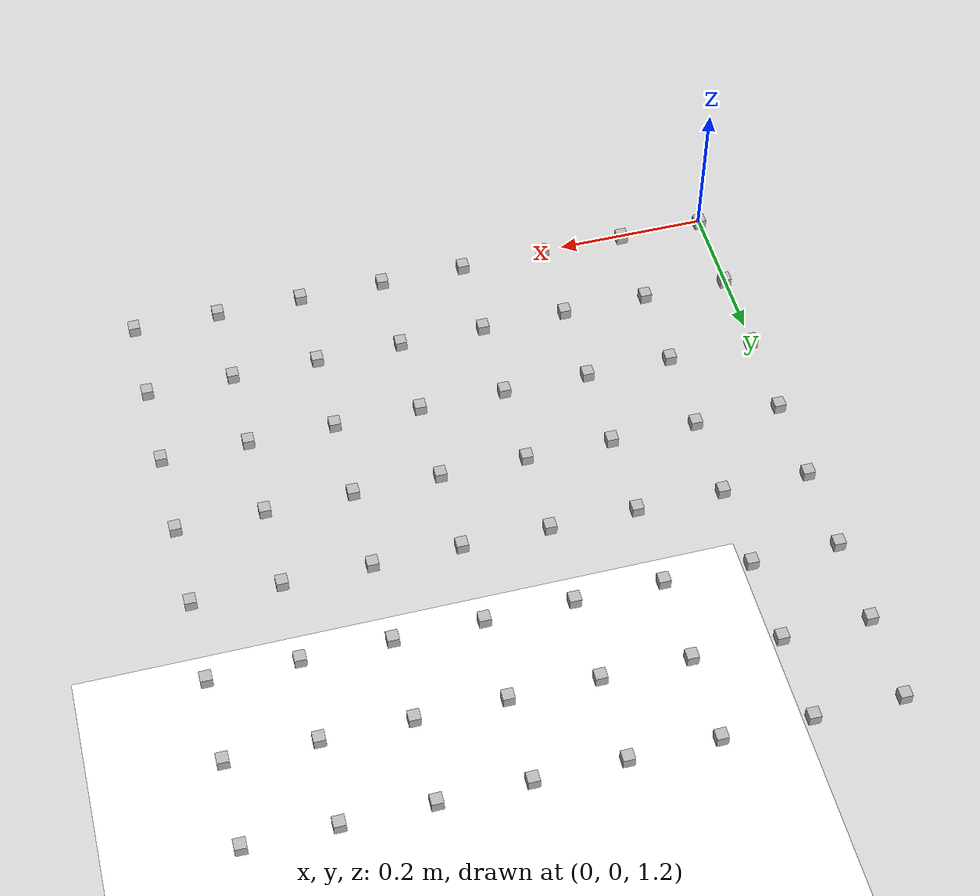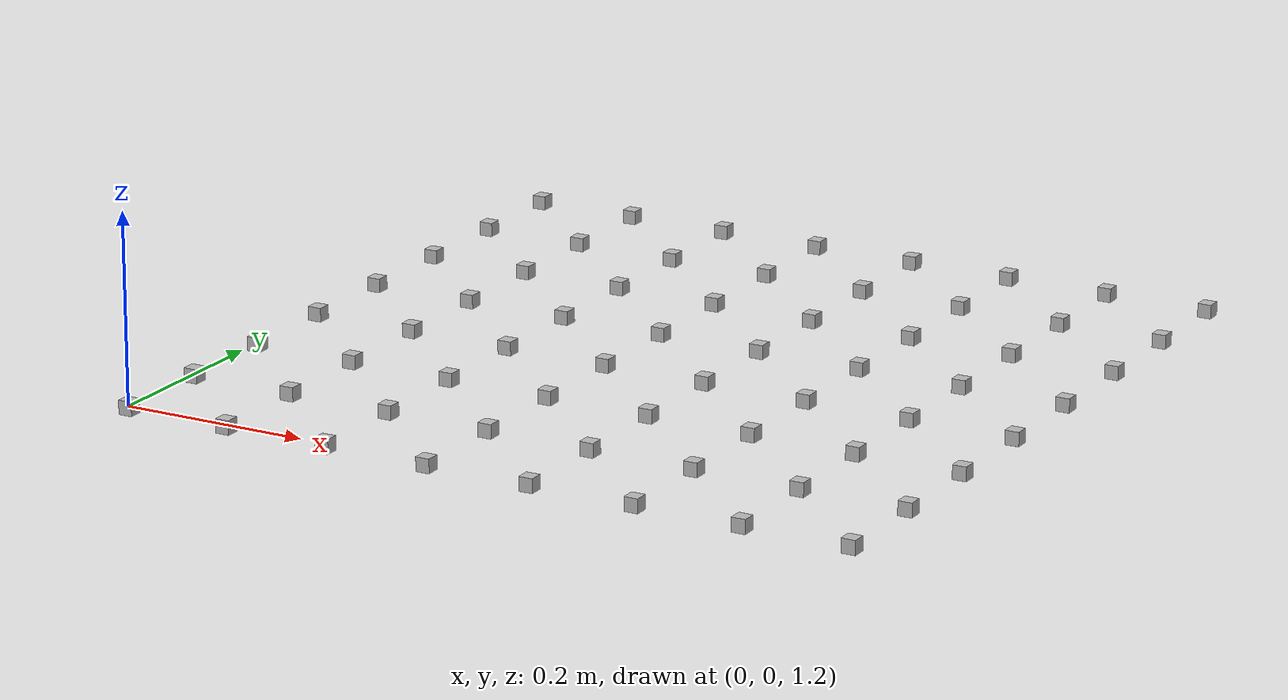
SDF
<!-- /sim/world_with_ground.sdf -->
<sdf version="1.7">
  <world name="default">
    <gravity>0 0 -9.81</gravity>

    <!-- Simple sun -->
    <light name="sun" type="directional">
      <cast_shadows>true</cast_shadows>
      <pose>0 0 10 0 0 0</pose>
      <direction>-0.5 0.5 -1</direction>
      <diffuse>1 1 1 1</diffuse>
      <specular>0.1 0.1 0.1 1</specular>
    </light>

    <!-- Ground plane -->
    <model name="ground">
      <static>true</static>
      <link name="ground_link">
        <collision name="ground_col">
          <geometry>
            <plane><normal>0 0 1</normal><size>200 200</size></plane>
          </geometry>
        </collision>
        <visual name="ground_vis">
          <geometry>
            <plane><normal>0 0 1</normal><size>200 200</size></plane>
          </geometry>
          <material>

                  <ambient>1 1 1 1</ambient>
        <diffuse>1 1 1 1</diffuse>
        <specular>0.1 0.1 0.1 1</specular>
        <emissive>0 0 0 1</emissive>

          </material>
        </visual>
      </link>
    </model>

    <!-- Include YOUR model from the mounted folder -->
    <include>

   <uri>file:///sim/mesh/spring_damper_mesh.sdf</uri>
      <!-- optional: place it -->
      <pose>0 0 0 0 0 0</pose>
    </include>
  </world>
</sdf>

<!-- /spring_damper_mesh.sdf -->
<sdf version="1.7">
  <model name="spring_damper_mesh">
    <static>false</static>
    <link name="mass_x0_y0">
      <pose>0.0 0.0 1.2 0 0 0</pose>
      <inertial>
        <mass>0.0328125</mass>
        <inertia>
          <ixx>1e-5</ixx>
          <ixy>0</ixy>
          <ixz>0</ixz>
          <iyy>1e-5</iyy>
          <iyz>0</iyz>
          <izz>1e-5</izz>
        </inertia>
      </inertial>
      <collision name="collision_x0_y0">
        <geometry>
          <sphere>
            <radius>0.001</radius>
          </sphere>
        </geometry>
      </collision>
      <visual name="visual_x0_y0">
        <geometry>
          <box>
            <size>0.015 0.015 0.015</size>
          </box>
        </geometry>
      </visual>
    </link>
    <link name="mass_x1_y0">
      <pose>0.1142857142857143 0.0 1.2 0 0 0</pose>
      <inertial>
        <mass>0.0328125</mass>
        <inertia>
          <ixx>1e-5</ixx>
          <ixy>0</ixy>
          <ixz>0</ixz>
          <iyy>1e-5</iyy>
          <iyz>0</iyz>
          <izz>1e-5</izz>
        </inertia>
      </inertial>
      <collision name="collision_x1_y0">
        <geometry>
          <sphere>
            <radius>0.001</radius>
          </sphere>
        </geometry>
      </collision>
      <visual name="visual_x1_y0">
        <geometry>
          <box>
            <size>0.015 0.015 0.015</size>
          </box>
        </geometry>
      </visual>
    </link>
    <link name="mass_x2_y0">
      <pose>0.2285714285714286 0.0 1.2 0 0 0</pose>
      <inertial>
        <mass>0.0328125</mass>
        <inertia>
          <ixx>1e-5</ixx>
          <ixy>0</ixy>
          <ixz>0</ixz>
          <iyy>1e-5</iyy>
          <iyz>0</iyz>
          <izz>1e-5</izz>
        </inertia>
      </inertial>
      <collision name="collision_x2_y0">
        <geometry>
          <sphere>
            <radius>0.001</radius>
          </sphere>
        </geometry>
      </collision>
      <visual name="visual_x2_y0">
        <geometry>
          <box>
            <size>0.015 0.015 0.015</size>
          </box>
        </geometry>
      </visual>
    </link>
    <link name="mass_x3_y0">
      <pose>0.34285714285714286 0.0 1.2 0 0 0</pose>
      <inertial>
        <mass>0.0328125</mass>
        <inertia>
          <ixx>1e-5</ixx>
          <ixy>0</ixy>
          <ixz>0</ixz>
          <iyy>1e-5</iyy>
          <iyz>0</iyz>
          <izz>1e-5</izz>
        </inertia>
      </inertial>
      <collision name="collision_x3_y0">
        <geometry>
          <sphere>
            <radius>0.001</radius>
          </sphere>
        </geometry>
      </collision>
      <visual name="visual_x3_y0">
        <geometry>
          <box>
            <size>0.015 0.015 0.015</size>
          </box>
        </geometry>
      </visual>
    </link>
    <link name="mass_x4_y0">
      <pose>0.4571428571428572 0.0 1.2 0 0 0</pose>
      <inertial>
        <mass>0.0328125</mass>
        <inertia>
          <ixx>1e-5</ixx>
          <ixy>0</ixy>
          <ixz>0</ixz>
          <iyy>1e-5</iyy>
          <iyz>0</iyz>
          <izz>1e-5</izz>
        </inertia>
      </inertial>
      <collision name="collision_x4_y0">
        <geometry>
          <sphere>
            <radius>0.001</radius>
          </sphere>
        </geometry>
      </collision>
      <visual name="visual_x4_y0">
        <geometry>
          <box>
            <size>0.015 0.015 0.015</size>
          </box>
        </geometry>
      </visual>
    </link>
    <link name="mass_x5_y0">
      <pose>0.5714285714285715 0.0 1.2 0 0 0</pose>
      <inertial>
        <mass>0.0328125</mass>
        <inertia>
          <ixx>1e-5</ixx>
          <ixy>0</ixy>
          <ixz>0</ixz>
          <iyy>1e-5</iyy>
          <iyz>0</iyz>
          <izz>1e-5</izz>
        </inertia>
      </inertial>
      <collision name="collision_x5_y0">
        <geometry>
          <sphere>
            <radius>0.001</radius>
          </sphere>
        </geometry>
      </collision>
      <visual name="visual_x5_y0">
        <geometry>
          <box>
            <size>0.015 0.015 0.015</size>
          </box>
        </geometry>
      </visual>
    </link>
    <link name="mass_x6_y0">
      <pose>0.6857142857142857 0.0 1.2 0 0 0</pose>
      <inertial>
        <mass>0.0328125</mass>
        <inertia>
          <ixx>1e-5</ixx>
          <ixy>0</ixy>
          <ixz>0</ixz>
          <iyy>1e-5</iyy>
          <iyz>0</iyz>
          <izz>1e-5</izz>
        </inertia>
      </inertial>
      <collision name="collision_x6_y0">
        <geometry>
          <sphere>
            <radius>0.001</radius>
          </sphere>
        </geometry>
      </collision>
      <visual name="visual_x6_y0">
        <geometry>
          <box>
            <size>0.015 0.015 0.015</size>
          </box>
        </geometry>
      </visual>
    </link>
    <link name="mass_x7_y0">
      <pose>0.8 0.0 1.2 0 0 0</pose>
      <inertial>
        <mass>0.0328125</mass>
        <inertia>
          <ixx>1e-5</ixx>
          <ixy>0</ixy>
          <ixz>0</ixz>
          <iyy>1e-5</iyy>
          <iyz>0</iyz>
          <izz>1e-5</izz>
        </inertia>
      </inertial>
      <collision name="collision_x7_y0">
        <geometry>
          <sphere>
            <radius>0.001</radius>
          </sphere>
        </geometry>
      </collision>
      <visual name="visual_x7_y0">
        <geometry>
          <box>
            <size>0.015 0.015 0.015</size>
          </box>
        </geometry>
      </visual>
    </link>
    <link name="mass_x0_y1">
      <pose>0.0 0.1142857142857143 1.2 0 0 0</pose>
      <inertial>
        <mass>0.0328125</mass>
        <inertia>
          <ixx>1e-5</ixx>
          <ixy>0</ixy>
          <ixz>0</ixz>
          <iyy>1e-5</iyy>
          <iyz>0</iyz>
          <izz>1e-5</izz>
        </inertia>
      </inertial>
      <collision name="collision_x0_y1">
        <geometry>
          <sphere>
            <radius>0.001</radius>
          </sphere>
        </geometry>
      </collision>
      <visual name="visual_x0_y1">
        <geometry>
          <box>
            <size>0.015 0.015 0.015</size>
          </box>
        </geometry>
      </visual>
    </link>
    <link name="mass_x1_y1">
      <pose>0.1142857142857143 0.1142857142857143 1.2 0 0 0</pose>
      <inertial>
        <mass>0.0328125</mass>
        <inertia>
          <ixx>1e-5</ixx>
          <ixy>0</ixy>
          <ixz>0</ixz>
          <iyy>1e-5</iyy>
          <iyz>0</iyz>
          <izz>1e-5</izz>
        </inertia>
      </inertial>
      <collision name="collision_x1_y1">
        <geometry>
          <sphere>
            <radius>0.001</radius>
          </sphere>
        </geometry>
      </collision>
      <visual name="visual_x1_y1">
        <geometry>
          <box>
            <size>0.015 0.015 0.015</size>
          </box>
        </geometry>
      </visual>
    </link>
    <link name="mass_x2_y1">
      <pose>0.2285714285714286 0.1142857142857143 1.2 0 0 0</pose>
      <inertial>
        <mass>0.0328125</mass>
        <inertia>
          <ixx>1e-5</ixx>
          <ixy>0</ixy>
          <ixz>0</ixz>
          <iyy>1e-5</iyy>
          <iyz>0</iyz>
          <izz>1e-5</izz>
        </inertia>
      </inertial>
      <collision name="collision_x2_y1">
        <geometry>
          <sphere>
            <radius>0.001</radius>
          </sphere>
        </geometry>
      </collision>
      <visual name="visual_x2_y1">
        <geometry>
          <box>
            <size>0.015 0.015 0.015</size>
          </box>
        </geometry>
      </visual>
    </link>
    <link name="mass_x3_y1">
      <pose>0.34285714285714286 0.1142857142857143 1.2 0 0 0</pose>
      <inertial>
        <mass>0.0328125</mass>
        <inertia>
          <ixx>1e-5</ixx>
          <ixy>0</ixy>
          <ixz>0</ixz>
          <iyy>1e-5</iyy>
          <iyz>0</iyz>
          <izz>1e-5</izz>
        </inertia>
      </inertial>
      <collision name="collision_x3_y1">
        <geometry>
          <sphere>
            <radius>0.001</radius>
          </sphere>
        </geometry>
      </collision>
      <visual name="visual_x3_y1">
        <geometry>
          <box>
            <size>0.015 0.015 0.015</size>
          </box>
        </geometry>
      </visual>
    </link>
    <link name="mass_x4_y1">
      <pose>0.4571428571428572 0.1142857142857143 1.2 0 0 0</pose>
      <inertial>
        <mass>0.0328125</mass>
        <inertia>
          <ixx>1e-5</ixx>
          <ixy>0</ixy>
          <ixz>0</ixz>
          <iyy>1e-5</iyy>
          <iyz>0</iyz>
          <izz>1e-5</izz>
        </inertia>
      </inertial>
      <collision name="collision_x4_y1">
        <geometry>
          <sphere>
            <radius>0.001</radius>
          </sphere>
        </geometry>
      </collision>
      <visual name="visual_x4_y1">
        <geometry>
          <box>
            <size>0.015 0.015 0.015</size>
          </box>
        </geometry>
      </visual>
    </link>
    <link name="mass_x5_y1">
      <pose>0.5714285714285715 0.1142857142857143 1.2 0 0 0</pose>
      <inertial>
        <mass>0.0328125</mass>
        <inertia>
          <ixx>1e-5</ixx>
          <ixy>0</ixy>
          <ixz>0</ixz>
          <iyy>1e-5</iyy>
          <iyz>0</iyz>
          <izz>1e-5</izz>
        </inertia>
      </inertial>
      <collision name="collision_x5_y1">
        <geometry>
          <sphere>
            <radius>0.001</radius>
          </sphere>
        </geometry>
      </collision>
      <visual name="visual_x5_y1">
        <geometry>
          <box>
            <size>0.015 0.015 0.015</size>
          </box>
        </geometry>
      </visual>
    </link>
    <link name="mass_x6_y1">
      <pose>0.6857142857142857 0.1142857142857143 1.2 0 0 0</pose>
      <inertial>
        <mass>0.0328125</mass>
        <inertia>
          <ixx>1e-5</ixx>
          <ixy>0</ixy>
          <ixz>0</ixz>
          <iyy>1e-5</iyy>
          <iyz>0</iyz>
          <izz>1e-5</izz>
        </inertia>
      </inertial>
      <collision name="collision_x6_y1">
        <geometry>
          <sphere>
            <radius>0.001</radius>
          </sphere>
        </geometry>
      </collision>
      <visual name="visual_x6_y1">
        <geometry>
          <box>
            <size>0.015 0.015 0.015</size>
          </box>
        </geometry>
      </visual>
    </link>
    <link name="mass_x7_y1">
      <pose>0.8 0.1142857142857143 1.2 0 0 0</pose>
      <inertial>
        <mass>0.0328125</mass>
        <inertia>
          <ixx>1e-5</ixx>
          <ixy>0</ixy>
          <ixz>0</ixz>
          <iyy>1e-5</iyy>
          <iyz>0</iyz>
          <izz>1e-5</izz>
        </inertia>
      </inertial>
      <collision name="collision_x7_y1">
        <geometry>
          <sphere>
            <radius>0.001</radius>
          </sphere>
        </geometry>
      </collision>
      <visual name="visual_x7_y1">
        <geometry>
          <box>
            <size>0.015 0.015 0.015</size>
          </box>
        </geometry>
      </visual>
    </link>
    <link name="mass_x0_y2">
      <pose>0.0 0.2285714285714286 1.2 0 0 0</pose>
      <inertial>
        <mass>0.0328125</mass>
        <inertia>
          <ixx>1e-5</ixx>
          <ixy>0</ixy>
          <ixz>0</ixz>
          <iyy>1e-5</iyy>
          <iyz>0</iyz>
          <izz>1e-5</izz>
        </inertia>
      </inertial>
      <collision name="collision_x0_y2">
        <geometry>
          <sphere>
            <radius>0.001</radius>
          </sphere>
        </geometry>
      </collision>
      <visual name="visual_x0_y2">
        <geometry>
          <box>
            <size>0.015 0.015 0.015</size>
          </box>
        </geometry>
      </visual>
    </link>
    <link name="mass_x1_y2">
      <pose>0.1142857142857143 0.2285714285714286 1.2 0 0 0</pose>
      <inertial>
        <mass>0.0328125</mass>
        <inertia>
          <ixx>1e-5</ixx>
          <ixy>0</ixy>
          <ixz>0</ixz>
          <iyy>1e-5</iyy>
          <iyz>0</iyz>
          <izz>1e-5</izz>
        </inertia>
      </inertial>
      <collision name="collision_x1_y2">
        <geometry>
          <sphere>
            <radius>0.001</radius>
          </sphere>
        </geometry>
      </collision>
      <visual name="visual_x1_y2">
        <geometry>
          <box>
            <size>0.015 0.015 0.015</size>
          </box>
        </geometry>
      </visual>
    </link>
    <link name="mass_x2_y2">
      <pose>0.2285714285714286 0.2285714285714286 1.2 0 0 0</pose>
      <inertial>
        <mass>0.0328125</mass>
        <inertia>
          <ixx>1e-5</ixx>
          <ixy>0</ixy>
          <ixz>0</ixz>
          <iyy>1e-5</iyy>
          <iyz>0</iyz>
          <izz>1e-5</izz>
        </inertia>
      </inertial>
      <collision name="collision_x2_y2">
        <geometry>
          <sphere>
            <radius>0.001</radius>
          </sphere>
        </geometry>
      </collision>
      <visual name="visual_x2_y2">
        <geometry>
          <box>
            <size>0.015 0.015 0.015</size>
          </box>
        </geometry>
      </visual>
    </link>
    <link name="mass_x3_y2">
      <pose>0.34285714285714286 0.2285714285714286 1.2 0 0 0</pose>
      <inertial>
        <mass>0.0328125</mass>
        <inertia>
          <ixx>1e-5</ixx>
          <ixy>0</ixy>
          <ixz>0</ixz>
          <iyy>1e-5</iyy>
          <iyz>0</iyz>
          <izz>1e-5</izz>
        </inertia>
      </inertial>
      <collision name="collision_x3_y2">
        <geometry>
          <sphere>
            <radius>0.001</radius>
          </sphere>
        </geometry>
      </collision>
      <visual name="visual_x3_y2">
        <geometry>
          <box>
            <size>0.015 0.015 0.015</size>
          </box>
        </geometry>
      </visual>
    </link>
    <link name="mass_x4_y2">
      <pose>0.4571428571428572 0.2285714285714286 1.2 0 0 0</pose>
      <inertial>
        <mass>0.0328125</mass>
        <inertia>
          <ixx>1e-5</ixx>
          <ixy>0</ixy>
          <ixz>0</ixz>
          <iyy>1e-5</iyy>
          <iyz>0</iyz>
          <izz>1e-5</izz>
        </inertia>
      </inertial>
      <collision name="collision_x4_y2">
        <geometry>
          <sphere>
            <radius>0.001</radius>
          </sphere>
        </geometry>
      </collision>
      <visual name="visual_x4_y2">
        <geometry>
          <box>
            <size>0.015 0.015 0.015</size>
          </box>
        </geometry>
      </visual>
    </link>
    <link name="mass_x5_y2">
      <pose>0.5714285714285715 0.2285714285714286 1.2 0 0 0</pose>
      <inertial>
        <mass>0.0328125</mass>
        <inertia>
          <ixx>1e-5</ixx>
          <ixy>0</ixy>
          <ixz>0</ixz>
          <iyy>1e-5</iyy>
          <iyz>0</iyz>
          <izz>1e-5</izz>
        </inertia>
      </inertial>
      <collision name="collision_x5_y2">
        <geometry>
          <sphere>
            <radius>0.001</radius>
          </sphere>
        </geometry>
      </collision>
      <visual name="visual_x5_y2">
        <geometry>
          <box>
            <size>0.015 0.015 0.015</size>
          </box>
        </geometry>
      </visual>
    </link>
    <link name="mass_x6_y2">
      <pose>0.6857142857142857 0.2285714285714286 1.2 0 0 0</pose>
      <inertial>
        <mass>0.0328125</mass>
        <inertia>
          <ixx>1e-5</ixx>
          <ixy>0</ixy>
          <ixz>0</ixz>
          <iyy>1e-5</iyy>
          <iyz>0</iyz>
          <izz>1e-5</izz>
        </inertia>
      </inertial>
      <collision name="collision_x6_y2">
        <geometry>
          <sphere>
            <radius>0.001</radius>
          </sphere>
        </geometry>
      </collision>
      <visual name="visual_x6_y2">
        <geometry>
          <box>
            <size>0.015 0.015 0.015</size>
          </box>
        </geometry>
      </visual>
    </link>
    <link name="mass_x7_y2">
      <pose>0.8 0.2285714285714286 1.2 0 0 0</pose>
      <inertial>
        <mass>0.0328125</mass>
        <inertia>
          <ixx>1e-5</ixx>
          <ixy>0</ixy>
          <ixz>0</ixz>
          <iyy>1e-5</iyy>
          <iyz>0</iyz>
          <izz>1e-5</izz>
        </inertia>
      </inertial>
      <collision name="collision_x7_y2">
        <geometry>
          <sphere>
            <radius>0.001</radius>
          </sphere>
        </geometry>
      </collision>
      <visual name="visual_x7_y2">
        <geometry>
          <box>
            <size>0.015 0.015 0.015</size>
          </box>
        </geometry>
      </visual>
    </link>
    <link name="mass_x0_y3">
      <pose>0.0 0.34285714285714286 1.2 0 0 0</pose>
      <inertial>
        <mass>0.0328125</mass>
        <inertia>
          <ixx>1e-5</ixx>
          <ixy>0</ixy>
          <ixz>0</ixz>
          <iyy>1e-5</iyy>
          <iyz>0</iyz>
          <izz>1e-5</izz>
        </inertia>
      </inertial>
      <collision name="collision_x0_y3">
        <geometry>
          <sphere>
            <radius>0.001</radius>
          </sphere>
        </geometry>
      </collision>
      <visual name="visual_x0_y3">
        <geometry>
          <box>
            <size>0.015 0.015 0.015</size>
          </box>
        </geometry>
      </visual>
    </link>
    <link name="mass_x1_y3">
      <pose>0.1142857142857143 0.34285714285714286 1.2 0 0 0</pose>
      <inertial>
        <mass>0.0328125</mass>
        <inertia>
          <ixx>1e-5</ixx>
          <ixy>0</ixy>
          <ixz>0</ixz>
          <iyy>1e-5</iyy>
          <iyz>0</iyz>
          <izz>1e-5</izz>
        </inertia>
      </inertial>
      <collision name="collision_x1_y3">
        <geometry>
          <sphere>
            <radius>0.001</radius>
          </sphere>
        </geometry>
      </collision>
      <visual name="visual_x1_y3">
        <geometry>
          <box>
            <size>0.015 0.015 0.015</size>
          </box>
        </geometry>
      </visual>
    </link>
    <link name="mass_x2_y3">
      <pose>0.2285714285714286 0.34285714285714286 1.2 0 0 0</pose>
      <inertial>
        <mass>0.0328125</mass>
        <inertia>
          <ixx>1e-5</ixx>
          <ixy>0</ixy>
          <ixz>0</ixz>
          <iyy>1e-5</iyy>
          <iyz>0</iyz>
          <izz>1e-5</izz>
        </inertia>
      </inertial>
      <collision name="collision_x2_y3">
        <geometry>
          <sphere>
            <radius>0.001</radius>
          </sphere>
        </geometry>
      </collision>
      <visual name="visual_x2_y3">
        <geometry>
          <box>
            <size>0.015 0.015 0.015</size>
          </box>
        </geometry>
      </visual>
    </link>
    <link name="mass_x3_y3">
      <pose>0.34285714285714286 0.34285714285714286 1.2 0 0 0</pose>
      <inertial>
        <mass>0.0328125</mass>
        <inertia>
          <ixx>1e-5</ixx>
          <ixy>0</ixy>
          <ixz>0</ixz>
          <iyy>1e-5</iyy>
          <iyz>0</iyz>
          <izz>1e-5</izz>
        </inertia>
      </inertial>
      <collision name="collision_x3_y3">
        <geometry>
          <sphere>
            <radius>0.001</radius>
          </sphere>
        </geometry>
      </collision>
      <visual name="visual_x3_y3">
        <geometry>
          <box>
            <size>0.015 0.015 0.015</size>
          </box>
        </geometry>
      </visual>
    </link>
    <link name="mass_x4_y3">
      <pose>0.4571428571428572 0.34285714285714286 1.2 0 0 0</pose>
      <inertial>
        <mass>0.0328125</mass>
        <inertia>
          <ixx>1e-5</ixx>
          <ixy>0</ixy>
          <ixz>0</ixz>
          <iyy>1e-5</iyy>
          <iyz>0</iyz>
          <izz>1e-5</izz>
        </inertia>
      </inertial>
      <collision name="collision_x4_y3">
        <geometry>
          <sphere>
            <radius>0.001</radius>
          </sphere>
        </geometry>
      </collision>
      <visual name="visual_x4_y3">
        <geometry>
          <box>
            <size>0.015 0.015 0.015</size>
          </box>
        </geometry>
      </visual>
    </link>
    <link name="mass_x5_y3">
      <pose>0.5714285714285715 0.34285714285714286 1.2 0 0 0</pose>
      <inertial>
        <mass>0.0328125</mass>
        <inertia>
          <ixx>1e-5</ixx>
          <ixy>0</ixy>
          <ixz>0</ixz>
          <iyy>1e-5</iyy>
          <iyz>0</iyz>
          <izz>1e-5</izz>
        </inertia>
      </inertial>
      <collision name="collision_x5_y3">
        <geometry>
          <sphere>
            <radius>0.001</radius>
          </sphere>
        </geometry>
      </collision>
      <visual name="visual_x5_y3">
        <geometry>
          <box>
            <size>0.015 0.015 0.015</size>
          </box>
        </geometry>
      </visual>
    </link>
    <link name="mass_x6_y3">
      <pose>0.6857142857142857 0.34285714285714286 1.2 0 0 0</pose>
      <inertial>
        <mass>0.0328125</mass>
        <inertia>
          <ixx>1e-5</ixx>
          <ixy>0</ixy>
          <ixz>0</ixz>
          <iyy>1e-5</iyy>
          <iyz>0</iyz>
          <izz>1e-5</izz>
        </inertia>
      </inertial>
      <collision name="collision_x6_y3">
        <geometry>
          <sphere>
            <radius>0.001</radius>
          </sphere>
        </geometry>
      </collision>
      <visual name="visual_x6_y3">
        <geometry>
          <box>
            <size>0.015 0.015 0.015</size>
          </box>
        </geometry>
      </visual>
    </link>
    <link name="mass_x7_y3">
      <pose>0.8 0.34285714285714286 1.2 0 0 0</pose>
      <inertial>
        <mass>0.0328125</mass>
        <inertia>
          <ixx>1e-5</ixx>
          <ixy>0</ixy>
          <ixz>0</ixz>
          <iyy>1e-5</iyy>
          <iyz>0</iyz>
          <izz>1e-5</izz>
        </inertia>
      </inertial>
      <collision name="collision_x7_y3">
        <geometry>
          <sphere>
            <radius>0.001</radius>
          </sphere>
        </geometry>
      </collision>
      <visual name="visual_x7_y3">
        <geometry>
          <box>
            <size>0.015 0.015 0.015</size>
          </box>
        </geometry>
      </visual>
    </link>
    <link name="mass_x0_y4">
      <pose>0.0 0.4571428571428572 1.2 0 0 0</pose>
      <inertial>
        <mass>0.0328125</mass>
        <inertia>
          <ixx>1e-5</ixx>
          <ixy>0</ixy>
          <ixz>0</ixz>
          <iyy>1e-5</iyy>
          <iyz>0</iyz>
          <izz>1e-5</izz>
        </inertia>
      </inertial>
      <collision name="collision_x0_y4">
        <geometry>
          <sphere>
            <radius>0.001</radius>
          </sphere>
        </geometry>
      </collision>
      <visual name="visual_x0_y4">
        <geometry>
          <box>
            <size>0.015 0.015 0.015</size>
          </box>
        </geometry>
      </visual>
    </link>
    <link name="mass_x1_y4">
      <pose>0.1142857142857143 0.4571428571428572 1.2 0 0 0</pose>
      <inertial>
        <mass>0.0328125</mass>
        <inertia>
          <ixx>1e-5</ixx>
          <ixy>0</ixy>
          <ixz>0</ixz>
          <iyy>1e-5</iyy>
          <iyz>0</iyz>
          <izz>1e-5</izz>
        </inertia>
      </inertial>
      <collision name="collision_x1_y4">
        <geometry>
          <sphere>
            <radius>0.001</radius>
          </sphere>
        </geometry>
      </collision>
      <visual name="visual_x1_y4">
        <geometry>
          <box>
            <size>0.015 0.015 0.015</size>
          </box>
        </geometry>
      </visual>
    </link>
    <link name="mass_x2_y4">
      <pose>0.2285714285714286 0.4571428571428572 1.2 0 0 0</pose>
      <inertial>
        <mass>0.0328125</mass>
        <inertia>
          <ixx>1e-5</ixx>
          <ixy>0</ixy>
          <ixz>0</ixz>
          <iyy>1e-5</iyy>
          <iyz>0</iyz>
          <izz>1e-5</izz>
        </inertia>
      </inertial>
      <collision name="collision_x2_y4">
        <geometry>
          <sphere>
            <radius>0.001</radius>
          </sphere>
        </geometry>
      </collision>
      <visual name="visual_x2_y4">
        <geometry>
          <box>
            <size>0.015 0.015 0.015</size>
          </box>
        </geometry>
      </visual>
    </link>
    <link name="mass_x3_y4">
      <pose>0.34285714285714286 0.4571428571428572 1.2 0 0 0</pose>
      <inertial>
        <mass>0.0328125</mass>
        <inertia>
          <ixx>1e-5</ixx>
          <ixy>0</ixy>
          <ixz>0</ixz>
          <iyy>1e-5</iyy>
          <iyz>0</iyz>
          <izz>1e-5</izz>
        </inertia>
      </inertial>
      <collision name="collision_x3_y4">
        <geometry>
          <sphere>
            <radius>0.001</radius>
          </sphere>
        </geometry>
      </collision>
      <visual name="visual_x3_y4">
        <geometry>
          <box>
            <size>0.015 0.015 0.015</size>
          </box>
        </geometry>
      </visual>
    </link>
    <link name="mass_x4_y4">
      <pose>0.4571428571428572 0.4571428571428572 1.2 0 0 0</pose>
      <inertial>
        <mass>0.0328125</mass>
        <inertia>
          <ixx>1e-5</ixx>
          <ixy>0</ixy>
          <ixz>0</ixz>
          <iyy>1e-5</iyy>
          <iyz>0</iyz>
          <izz>1e-5</izz>
        </inertia>
      </inertial>
      <collision name="collision_x4_y4">
        <geometry>
          <sphere>
            <radius>0.001</radius>
          </sphere>
        </geometry>
      </collision>
      <visual name="visual_x4_y4">
        <geometry>
          <box>
            <size>0.015 0.015 0.015</size>
          </box>
        </geometry>
      </visual>
    </link>
    <link name="mass_x5_y4">
      <pose>0.5714285714285715 0.4571428571428572 1.2 0 0 0</pose>
      <inertial>
        <mass>0.0328125</mass>
        <inertia>
          <ixx>1e-5</ixx>
          <ixy>0</ixy>
          <ixz>0</ixz>
          <iyy>1e-5</iyy>
          <iyz>0</iyz>
          <izz>1e-5</izz>
        </inertia>
      </inertial>
      <collision name="collision_x5_y4">
        <geometry>
          <sphere>
            <radius>0.001</radius>
          </sphere>
        </geometry>
      </collision>
      <visual name="visual_x5_y4">
        <geometry>
          <box>
            <size>0.015 0.015 0.015</size>
          </box>
        </geometry>
      </visual>
    </link>
    <link name="mass_x6_y4">
      <pose>0.6857142857142857 0.4571428571428572 1.2 0 0 0</pose>
      <inertial>
        <mass>0.0328125</mass>
        <inertia>
          <ixx>1e-5</ixx>
          <ixy>0</ixy>
          <ixz>0</ixz>
          <iyy>1e-5</iyy>
          <iyz>0</iyz>
          <izz>1e-5</izz>
        </inertia>
      </inertial>
      <collision name="collision_x6_y4">
        <geometry>
          <sphere>
            <radius>0.001</radius>
          </sphere>
        </geometry>
      </collision>
      <visual name="visual_x6_y4">
        <geometry>
          <box>
            <size>0.015 0.015 0.015</size>
          </box>
        </geometry>
      </visual>
    </link>
    <link name="mass_x7_y4">
      <pose>0.8 0.4571428571428572 1.2 0 0 0</pose>
      <inertial>
        <mass>0.0328125</mass>
        <inertia>
          <ixx>1e-5</ixx>
          <ixy>0</ixy>
          <ixz>0</ixz>
          <iyy>1e-5</iyy>
          <iyz>0</iyz>
          <izz>1e-5</izz>
        </inertia>
      </inertial>
      <collision name="collision_x7_y4">
        <geometry>
          <sphere>
            <radius>0.001</radius>
          </sphere>
        </geometry>
      </collision>
      <visual name="visual_x7_y4">
        <geometry>
          <box>
            <size>0.015 0.015 0.015</size>
          </box>
        </geometry>
      </visual>
    </link>
    <link name="mass_x0_y5">
      <pose>0.0 0.5714285714285715 1.2 0 0 0</pose>
      <inertial>
        <mass>0.0328125</mass>
        <inertia>
          <ixx>1e-5</ixx>
          <ixy>0</ixy>
          <ixz>0</ixz>
          <iyy>1e-5</iyy>
          <iyz>0</iyz>
          <izz>1e-5</izz>
        </inertia>
      </inertial>
      <collision name="collision_x0_y5">
        <geometry>
          <sphere>
            <radius>0.001</radius>
          </sphere>
        </geometry>
      </collision>
      <visual name="visual_x0_y5">
        <geometry>
          <box>
            <size>0.015 0.015 0.015</size>
          </box>
        </geometry>
      </visual>
    </link>
    <link name="mass_x1_y5">
      <pose>0.1142857142857143 0.5714285714285715 1.2 0 0 0</pose>
      <inertial>
        <mass>0.0328125</mass>
        <inertia>
          <ixx>1e-5</ixx>
          <ixy>0</ixy>
          <ixz>0</ixz>
          <iyy>1e-5</iyy>
          <iyz>0</iyz>
          <izz>1e-5</izz>
        </inertia>
      </inertial>
      <collision name="collision_x1_y5">
        <geometry>
          <sphere>
            <radius>0.001</radius>
          </sphere>
        </geometry>
      </collision>
      <visual name="visual_x1_y5">
        <geometry>
          <box>
            <size>0.015 0.015 0.015</size>
          </box>
        </geometry>
      </visual>
    </link>
    <link name="mass_x2_y5">
      <pose>0.2285714285714286 0.5714285714285715 1.2 0 0 0</pose>
      <inertial>
        <mass>0.0328125</mass>
        <inertia>
          <ixx>1e-5</ixx>
          <ixy>0</ixy>
          <ixz>0</ixz>
          <iyy>1e-5</iyy>
          <iyz>0</iyz>
          <izz>1e-5</izz>
        </inertia>
      </inertial>
      <collision name="collision_x2_y5">
        <geometry>
          <sphere>
            <radius>0.001</radius>
          </sphere>
        </geometry>
      </collision>
      <visual name="visual_x2_y5">
        <geometry>
          <box>
            <size>0.015 0.015 0.015</size>
          </box>
        </geometry>
      </visual>
    </link>
    <link name="mass_x3_y5">
      <pose>0.34285714285714286 0.5714285714285715 1.2 0 0 0</pose>
      <inertial>
        <mass>0.0328125</mass>
        <inertia>
          <ixx>1e-5</ixx>
          <ixy>0</ixy>
          <ixz>0</ixz>
          <iyy>1e-5</iyy>
          <iyz>0</iyz>
          <izz>1e-5</izz>
        </inertia>
      </inertial>
      <collision name="collision_x3_y5">
        <geometry>
          <sphere>
            <radius>0.001</radius>
          </sphere>
        </geometry>
      </collision>
      <visual name="visual_x3_y5">
        <geometry>
          <box>
            <size>0.015 0.015 0.015</size>
          </box>
        </geometry>
      </visual>
    </link>
    <link name="mass_x4_y5">
      <pose>0.4571428571428572 0.5714285714285715 1.2 0 0 0</pose>
      <inertial>
        <mass>0.0328125</mass>
        <inertia>
          <ixx>1e-5</ixx>
          <ixy>0</ixy>
          <ixz>0</ixz>
          <iyy>1e-5</iyy>
          <iyz>0</iyz>
          <izz>1e-5</izz>
        </inertia>
      </inertial>
      <collision name="collision_x4_y5">
        <geometry>
          <sphere>
            <radius>0.001</radius>
          </sphere>
        </geometry>
      </collision>
      <visual name="visual_x4_y5">
        <geometry>
          <box>
            <size>0.015 0.015 0.015</size>
          </box>
        </geometry>
      </visual>
    </link>
    <link name="mass_x5_y5">
      <pose>0.5714285714285715 0.5714285714285715 1.2 0 0 0</pose>
      <inertial>
        <mass>0.0328125</mass>
        <inertia>
          <ixx>1e-5</ixx>
          <ixy>0</ixy>
          <ixz>0</ixz>
          <iyy>1e-5</iyy>
          <iyz>0</iyz>
          <izz>1e-5</izz>
        </inertia>
      </inertial>
      <collision name="collision_x5_y5">
        <geometry>
          <sphere>
            <radius>0.001</radius>
          </sphere>
        </geometry>
      </collision>
      <visual name="visual_x5_y5">
        <geometry>
          <box>
            <size>0.015 0.015 0.015</size>
          </box>
        </geometry>
      </visual>
    </link>
    <link name="mass_x6_y5">
      <pose>0.6857142857142857 0.5714285714285715 1.2 0 0 0</pose>
      <inertial>
        <mass>0.0328125</mass>
        <inertia>
          <ixx>1e-5</ixx>
          <ixy>0</ixy>
          <ixz>0</ixz>
          <iyy>1e-5</iyy>
          <iyz>0</iyz>
          <izz>1e-5</izz>
        </inertia>
      </inertial>
      <collision name="collision_x6_y5">
        <geometry>
          <sphere>
            <radius>0.001</radius>
          </sphere>
        </geometry>
      </collision>
      <visual name="visual_x6_y5">
        <geometry>
          <box>
            <size>0.015 0.015 0.015</size>
          </box>
        </geometry>
      </visual>
    </link>
    <link name="mass_x7_y5">
      <pose>0.8 0.5714285714285715 1.2 0 0 0</pose>
      <inertial>
        <mass>0.0328125</mass>
        <inertia>
          <ixx>1e-5</ixx>
          <ixy>0</ixy>
          <ixz>0</ixz>
          <iyy>1e-5</iyy>
          <iyz>0</iyz>
          <izz>1e-5</izz>
        </inertia>
      </inertial>
      <collision name="collision_x7_y5">
        <geometry>
          <sphere>
            <radius>0.001</radius>
          </sphere>
        </geometry>
      </collision>
      <visual name="visual_x7_y5">
        <geometry>
          <box>
            <size>0.015 0.015 0.015</size>
          </box>
        </geometry>
      </visual>
    </link>
    <link name="mass_x0_y6">
      <pose>0.0 0.6857142857142857 1.2 0 0 0</pose>
      <inertial>
        <mass>0.0328125</mass>
        <inertia>
          <ixx>1e-5</ixx>
          <ixy>0</ixy>
          <ixz>0</ixz>
          <iyy>1e-5</iyy>
          <iyz>0</iyz>
          <izz>1e-5</izz>
        </inertia>
      </inertial>
      <collision name="collision_x0_y6">
        <geometry>
          <sphere>
            <radius>0.001</radius>
          </sphere>
        </geometry>
      </collision>
      <visual name="visual_x0_y6">
        <geometry>
          <box>
            <size>0.015 0.015 0.015</size>
          </box>
        </geometry>
      </visual>
    </link>
    <link name="mass_x1_y6">
      <pose>0.1142857142857143 0.6857142857142857 1.2 0 0 0</pose>
      <inertial>
        <mass>0.0328125</mass>
        <inertia>
          <ixx>1e-5</ixx>
          <ixy>0</ixy>
          <ixz>0</ixz>
          <iyy>1e-5</iyy>
          <iyz>0</iyz>
          <izz>1e-5</izz>
        </inertia>
      </inertial>
      <collision name="collision_x1_y6">
        <geometry>
          <sphere>
            <radius>0.001</radius>
          </sphere>
        </geometry>
      </collision>
      <visual name="visual_x1_y6">
        <geometry>
          <box>
            <size>0.015 0.015 0.015</size>
          </box>
        </geometry>
      </visual>
    </link>
    <link name="mass_x2_y6">
      <pose>0.2285714285714286 0.6857142857142857 1.2 0 0 0</pose>
      <inertial>
        <mass>0.0328125</mass>
        <inertia>
          <ixx>1e-5</ixx>
          <ixy>0</ixy>
          <ixz>0</ixz>
          <iyy>1e-5</iyy>
          <iyz>0</iyz>
          <izz>1e-5</izz>
        </inertia>
      </inertial>
      <collision name="collision_x2_y6">
        <geometry>
          <sphere>
            <radius>0.001</radius>
          </sphere>
        </geometry>
      </collision>
      <visual name="visual_x2_y6">
        <geometry>
          <box>
            <size>0.015 0.015 0.015</size>
          </box>
        </geometry>
      </visual>
    </link>
    <link name="mass_x3_y6">
      <pose>0.34285714285714286 0.6857142857142857 1.2 0 0 0</pose>
      <inertial>
        <mass>0.0328125</mass>
        <inertia>
          <ixx>1e-5</ixx>
          <ixy>0</ixy>
          <ixz>0</ixz>
          <iyy>1e-5</iyy>
          <iyz>0</iyz>
          <izz>1e-5</izz>
        </inertia>
      </inertial>
      <collision name="collision_x3_y6">
        <geometry>
          <sphere>
            <radius>0.001</radius>
          </sphere>
        </geometry>
      </collision>
      <visual name="visual_x3_y6">
        <geometry>
          <box>
            <size>0.015 0.015 0.015</size>
          </box>
        </geometry>
      </visual>
    </link>
    <link name="mass_x4_y6">
      <pose>0.4571428571428572 0.6857142857142857 1.2 0 0 0</pose>
      <inertial>
        <mass>0.0328125</mass>
        <inertia>
          <ixx>1e-5</ixx>
          <ixy>0</ixy>
          <ixz>0</ixz>
          <iyy>1e-5</iyy>
          <iyz>0</iyz>
          <izz>1e-5</izz>
        </inertia>
      </inertial>
      <collision name="collision_x4_y6">
        <geometry>
          <sphere>
            <radius>0.001</radius>
          </sphere>
        </geometry>
      </collision>
      <visual name="visual_x4_y6">
        <geometry>
          <box>
            <size>0.015 0.015 0.015</size>
          </box>
        </geometry>
      </visual>
    </link>
    <link name="mass_x5_y6">
      <pose>0.5714285714285715 0.6857142857142857 1.2 0 0 0</pose>
      <inertial>
        <mass>0.0328125</mass>
        <inertia>
          <ixx>1e-5</ixx>
          <ixy>0</ixy>
          <ixz>0</ixz>
          <iyy>1e-5</iyy>
          <iyz>0</iyz>
          <izz>1e-5</izz>
        </inertia>
      </inertial>
      <collision name="collision_x5_y6">
        <geometry>
          <sphere>
            <radius>0.001</radius>
          </sphere>
        </geometry>
      </collision>
      <visual name="visual_x5_y6">
        <geometry>
          <box>
            <size>0.015 0.015 0.015</size>
          </box>
        </geometry>
      </visual>
    </link>
    <link name="mass_x6_y6">
      <pose>0.6857142857142857 0.6857142857142857 1.2 0 0 0</pose>
      <inertial>
        <mass>0.0328125</mass>
        <inertia>
          <ixx>1e-5</ixx>
          <ixy>0</ixy>
          <ixz>0</ixz>
          <iyy>1e-5</iyy>
          <iyz>0</iyz>
          <izz>1e-5</izz>
        </inertia>
      </inertial>
      <collision name="collision_x6_y6">
        <geometry>
          <sphere>
            <radius>0.001</radius>
          </sphere>
        </geometry>
      </collision>
      <visual name="visual_x6_y6">
        <geometry>
          <box>
            <size>0.015 0.015 0.015</size>
          </box>
        </geometry>
      </visual>
    </link>
    <link name="mass_x7_y6">
      <pose>0.8 0.6857142857142857 1.2 0 0 0</pose>
      <inertial>
        <mass>0.0328125</mass>
        <inertia>
          <ixx>1e-5</ixx>
          <ixy>0</ixy>
          <ixz>0</ixz>
          <iyy>1e-5</iyy>
          <iyz>0</iyz>
          <izz>1e-5</izz>
        </inertia>
      </inertial>
      <collision name="collision_x7_y6">
        <geometry>
          <sphere>
            <radius>0.001</radius>
          </sphere>
        </geometry>
      </collision>
      <visual name="visual_x7_y6">
        <geometry>
          <box>
            <size>0.015 0.015 0.015</size>
          </box>
        </geometry>
      </visual>
    </link>
    <link name="mass_x0_y7">
      <pose>0.0 0.8 1.2 0 0 0</pose>
      <inertial>
        <mass>0.0328125</mass>
        <inertia>
          <ixx>1e-5</ixx>
          <ixy>0</ixy>
          <ixz>0</ixz>
          <iyy>1e-5</iyy>
          <iyz>0</iyz>
          <izz>1e-5</izz>
        </inertia>
      </inertial>
      <collision name="collision_x0_y7">
        <geometry>
          <sphere>
            <radius>0.001</radius>
          </sphere>
        </geometry>
      </collision>
      <visual name="visual_x0_y7">
        <geometry>
          <box>
            <size>0.015 0.015 0.015</size>
          </box>
        </geometry>
      </visual>
    </link>
    <link name="mass_x1_y7">
      <pose>0.1142857142857143 0.8 1.2 0 0 0</pose>
      <inertial>
        <mass>0.0328125</mass>
        <inertia>
          <ixx>1e-5</ixx>
          <ixy>0</ixy>
          <ixz>0</ixz>
          <iyy>1e-5</iyy>
          <iyz>0</iyz>
          <izz>1e-5</izz>
        </inertia>
      </inertial>
      <collision name="collision_x1_y7">
        <geometry>
          <sphere>
            <radius>0.001</radius>
          </sphere>
        </geometry>
      </collision>
      <visual name="visual_x1_y7">
        <geometry>
          <box>
            <size>0.015 0.015 0.015</size>
          </box>
        </geometry>
      </visual>
    </link>
    <link name="mass_x2_y7">
      <pose>0.2285714285714286 0.8 1.2 0 0 0</pose>
      <inertial>
        <mass>0.0328125</mass>
        <inertia>
          <ixx>1e-5</ixx>
          <ixy>0</ixy>
          <ixz>0</ixz>
          <iyy>1e-5</iyy>
          <iyz>0</iyz>
          <izz>1e-5</izz>
        </inertia>
      </inertial>
      <collision name="collision_x2_y7">
        <geometry>
          <sphere>
            <radius>0.001</radius>
          </sphere>
        </geometry>
      </collision>
      <visual name="visual_x2_y7">
        <geometry>
          <box>
            <size>0.015 0.015 0.015</size>
          </box>
        </geometry>
      </visual>
    </link>
    <link name="mass_x3_y7">
      <pose>0.34285714285714286 0.8 1.2 0 0 0</pose>
      <inertial>
        <mass>0.0328125</mass>
        <inertia>
          <ixx>1e-5</ixx>
          <ixy>0</ixy>
          <ixz>0</ixz>
          <iyy>1e-5</iyy>
          <iyz>0</iyz>
          <izz>1e-5</izz>
        </inertia>
      </inertial>
      <collision name="collision_x3_y7">
        <geometry>
          <sphere>
            <radius>0.001</radius>
          </sphere>
        </geometry>
      </collision>
      <visual name="visual_x3_y7">
        <geometry>
          <box>
            <size>0.015 0.015 0.015</size>
          </box>
        </geometry>
      </visual>
    </link>
    <link name="mass_x4_y7">
      <pose>0.4571428571428572 0.8 1.2 0 0 0</pose>
      <inertial>
        <mass>0.0328125</mass>
        <inertia>
          <ixx>1e-5</ixx>
          <ixy>0</ixy>
          <ixz>0</ixz>
          <iyy>1e-5</iyy>
          <iyz>0</iyz>
          <izz>1e-5</izz>
        </inertia>
      </inertial>
      <collision name="collision_x4_y7">
        <geometry>
          <sphere>
            <radius>0.001</radius>
          </sphere>
        </geometry>
      </collision>
      <visual name="visual_x4_y7">
        <geometry>
          <box>
            <size>0.015 0.015 0.015</size>
          </box>
        </geometry>
      </visual>
    </link>
    <link name="mass_x5_y7">
      <pose>0.5714285714285715 0.8 1.2 0 0 0</pose>
      <inertial>
        <mass>0.0328125</mass>
        <inertia>
          <ixx>1e-5</ixx>
          <ixy>0</ixy>
          <ixz>0</ixz>
          <iyy>1e-5</iyy>
          <iyz>0</iyz>
          <izz>1e-5</izz>
        </inertia>
      </inertial>
      <collision name="collision_x5_y7">
        <geometry>
          <sphere>
            <radius>0.001</radius>
          </sphere>
        </geometry>
      </collision>
      <visual name="visual_x5_y7">
        <geometry>
          <box>
            <size>0.015 0.015 0.015</size>
          </box>
        </geometry>
      </visual>
    </link>
    <link name="mass_x6_y7">
      <pose>0.6857142857142857 0.8 1.2 0 0 0</pose>
      <inertial>
        <mass>0.0328125</mass>
        <inertia>
          <ixx>1e-5</ixx>
          <ixy>0</ixy>
          <ixz>0</ixz>
          <iyy>1e-5</iyy>
          <iyz>0</iyz>
          <izz>1e-5</izz>
        </inertia>
      </inertial>
      <collision name="collision_x6_y7">
        <geometry>
          <sphere>
            <radius>0.001</radius>
          </sphere>
        </geometry>
      </collision>
      <visual name="visual_x6_y7">
        <geometry>
          <box>
            <size>0.015 0.015 0.015</size>
          </box>
        </geometry>
      </visual>
    </link>
    <link name="mass_x7_y7">
      <pose>0.8 0.8 1.2 0 0 0</pose>
      <inertial>
        <mass>0.0328125</mass>
        <inertia>
          <ixx>1e-5</ixx>
          <ixy>0</ixy>
          <ixz>0</ixz>
          <iyy>1e-5</iyy>
          <iyz>0</iyz>
          <izz>1e-5</izz>
        </inertia>
      </inertial>
      <collision name="collision_x7_y7">
        <geometry>
          <sphere>
            <radius>0.001</radius>
          </sphere>
        </geometry>
      </collision>
      <visual name="visual_x7_y7">
        <geometry>
          <box>
            <size>0.015 0.015 0.015</size>
          </box>
        </geometry>
      </visual>
    </link>
    <joint name="N_x0_y0_to_x1_y0" type="ball">
      <parent>mass_x0_y0</parent>
      <child>mass_x1_y0</child>
      <pose relative_to="mass_x1_y0">-0.05714285714285715 0 0 0 0 0</pose>
    </joint>
    <joint name="W_x0_y0_to_x0_y1" type="ball">
      <parent>mass_x0_y0</parent>
      <child>mass_x0_y1</child>
      <pose relative_to="mass_x0_y1">0 -0.05714285714285715 0 0 0 1.5707963267948966</pose>
    </joint>
    <joint name="NW_x0_y0_to_x1_y1" type="universal">
      <parent>mass_x0_y0</parent>
      <child>mass_x1_y1</child>
      <axis>
        <xyz>1 0 0</xyz>
        <dynamics>
          <damping>0.001</damping>
          <spring_stiffness>50</spring_stiffness>
        </dynamics>
      </axis>
      <axis2>
        <xyz>0 1 0</xyz>
        <dynamics>
          <damping>0.001</damping>
          <spring_stiffness>50</spring_stiffness>
        </dynamics>
      </axis2>
      <pose relative_to="mass_x1_y1">-0.05714285714285715 -0.05714285714285715 0 0 0 0.7853981633974483</pose>
    </joint>
    <joint name="N_x1_y0_to_x2_y0" type="ball">
      <parent>mass_x1_y0</parent>
      <child>mass_x2_y0</child>
      <pose relative_to="mass_x2_y0">-0.05714285714285715 0 0 0 0 0</pose>
    </joint>
    <joint name="W_x1_y0_to_x1_y1" type="ball">
      <parent>mass_x1_y0</parent>
      <child>mass_x1_y1</child>
      <pose relative_to="mass_x1_y1">0 -0.05714285714285715 0 0 0 1.5707963267948966</pose>
    </joint>
    <joint name="SW_x1_y0_to_x0_y1" type="universal">
      <parent>mass_x1_y0</parent>
      <child>mass_x0_y1</child>
      <axis>
        <xyz>1 0 0</xyz>
        <dynamics>
          <damping>0.001</damping>
          <spring_stiffness>50</spring_stiffness>
        </dynamics>
      </axis>
      <axis2>
        <xyz>0 1 0</xyz>
        <dynamics>
          <damping>0.001</damping>
          <spring_stiffness>50</spring_stiffness>
        </dynamics>
      </axis2>
      <pose relative_to="mass_x0_y1">0.05714285714285715 -0.05714285714285715 0 0 0 2.356194490192345</pose>
    </joint>
    <joint name="NW_x1_y0_to_x2_y1" type="universal">
      <parent>mass_x1_y0</parent>
      <child>mass_x2_y1</child>
      <axis>
        <xyz>1 0 0</xyz>
        <dynamics>
          <damping>0.001</damping>
          <spring_stiffness>50</spring_stiffness>
        </dynamics>
      </axis>
      <axis2>
        <xyz>0 1 0</xyz>
        <dynamics>
          <damping>0.001</damping>
          <spring_stiffness>50</spring_stiffness>
        </dynamics>
      </axis2>
      <pose relative_to="mass_x2_y1">-0.05714285714285715 -0.05714285714285715 0 0 0 0.7853981633974483</pose>
    </joint>
    <joint name="N_x2_y0_to_x3_y0" type="ball">
      <parent>mass_x2_y0</parent>
      <child>mass_x3_y0</child>
      <pose relative_to="mass_x3_y0">-0.05714285714285715 0 0 0 0 0</pose>
    </joint>
    <joint name="W_x2_y0_to_x2_y1" type="ball">
      <parent>mass_x2_y0</parent>
      <child>mass_x2_y1</child>
      <pose relative_to="mass_x2_y1">0 -0.05714285714285715 0 0 0 1.5707963267948966</pose>
    </joint>
    <joint name="SW_x2_y0_to_x1_y1" type="universal">
      <parent>mass_x2_y0</parent>
      <child>mass_x1_y1</child>
      <axis>
        <xyz>1 0 0</xyz>
        <dynamics>
          <damping>0.001</damping>
          <spring_stiffness>50</spring_stiffness>
        </dynamics>
      </axis>
      <axis2>
        <xyz>0 1 0</xyz>
        <dynamics>
          <damping>0.001</damping>
          <spring_stiffness>50</spring_stiffness>
        </dynamics>
      </axis2>
      <pose relative_to="mass_x1_y1">0.05714285714285715 -0.05714285714285715 0 0 0 2.356194490192345</pose>
    </joint>
    <joint name="NW_x2_y0_to_x3_y1" type="universal">
      <parent>mass_x2_y0</parent>
      <child>mass_x3_y1</child>
      <axis>
        <xyz>1 0 0</xyz>
        <dynamics>
          <damping>0.001</damping>
          <spring_stiffness>50</spring_stiffness>
        </dynamics>
      </axis>
      <axis2>
        <xyz>0 1 0</xyz>
        <dynamics>
          <damping>0.001</damping>
          <spring_stiffness>50</spring_stiffness>
        </dynamics>
      </axis2>
      <pose relative_to="mass_x3_y1">-0.05714285714285715 -0.05714285714285715 0 0 0 0.7853981633974483</pose>
    </joint>
    <joint name="N_x3_y0_to_x4_y0" type="ball">
      <parent>mass_x3_y0</parent>
      <child>mass_x4_y0</child>
      <pose relative_to="mass_x4_y0">-0.05714285714285715 0 0 0 0 0</pose>
    </joint>
    <joint name="W_x3_y0_to_x3_y1" type="ball">
      <parent>mass_x3_y0</parent>
      <child>mass_x3_y1</child>
      <pose relative_to="mass_x3_y1">0 -0.05714285714285715 0 0 0 1.5707963267948966</pose>
    </joint>
    <joint name="SW_x3_y0_to_x2_y1" type="universal">
      <parent>mass_x3_y0</parent>
      <child>mass_x2_y1</child>
      <axis>
        <xyz>1 0 0</xyz>
        <dynamics>
          <damping>0.001</damping>
          <spring_stiffness>50</spring_stiffness>
        </dynamics>
      </axis>
      <axis2>
        <xyz>0 1 0</xyz>
        <dynamics>
          <damping>0.001</damping>
          <spring_stiffness>50</spring_stiffness>
        </dynamics>
      </axis2>
      <pose relative_to="mass_x2_y1">0.05714285714285715 -0.05714285714285715 0 0 0 2.356194490192345</pose>
    </joint>
    <joint name="NW_x3_y0_to_x4_y1" type="universal">
      <parent>mass_x3_y0</parent>
      <child>mass_x4_y1</child>
      <axis>
        <xyz>1 0 0</xyz>
        <dynamics>
          <damping>0.001</damping>
          <spring_stiffness>50</spring_stiffness>
        </dynamics>
      </axis>
      <axis2>
        <xyz>0 1 0</xyz>
        <dynamics>
          <damping>0.001</damping>
          <spring_stiffness>50</spring_stiffness>
        </dynamics>
      </axis2>
      <pose relative_to="mass_x4_y1">-0.05714285714285715 -0.05714285714285715 0 0 0 0.7853981633974483</pose>
    </joint>
    <joint name="N_x4_y0_to_x5_y0" type="ball">
      <parent>mass_x4_y0</parent>
      <child>mass_x5_y0</child>
      <pose relative_to="mass_x5_y0">-0.05714285714285715 0 0 0 0 0</pose>
    </joint>
    <joint name="W_x4_y0_to_x4_y1" type="ball">
      <parent>mass_x4_y0</parent>
      <child>mass_x4_y1</child>
      <pose relative_to="mass_x4_y1">0 -0.05714285714285715 0 0 0 1.5707963267948966</pose>
    </joint>
    <joint name="SW_x4_y0_to_x3_y1" type="universal">
      <parent>mass_x4_y0</parent>
      <child>mass_x3_y1</child>
      <axis>
        <xyz>1 0 0</xyz>
        <dynamics>
          <damping>0.001</damping>
          <spring_stiffness>50</spring_stiffness>
        </dynamics>
      </axis>
      <axis2>
        <xyz>0 1 0</xyz>
        <dynamics>
          <damping>0.001</damping>
          <spring_stiffness>50</spring_stiffness>
        </dynamics>
      </axis2>
      <pose relative_to="mass_x3_y1">0.05714285714285715 -0.05714285714285715 0 0 0 2.356194490192345</pose>
    </joint>
    <joint name="NW_x4_y0_to_x5_y1" type="universal">
      <parent>mass_x4_y0</parent>
      <child>mass_x5_y1</child>
      <axis>
        <xyz>1 0 0</xyz>
        <dynamics>
          <damping>0.001</damping>
          <spring_stiffness>50</spring_stiffness>
        </dynamics>
      </axis>
      <axis2>
        <xyz>0 1 0</xyz>
        <dynamics>
          <damping>0.001</damping>
          <spring_stiffness>50</spring_stiffness>
        </dynamics>
      </axis2>
      <pose relative_to="mass_x5_y1">-0.05714285714285715 -0.05714285714285715 0 0 0 0.7853981633974483</pose>
    </joint>
    <joint name="N_x5_y0_to_x6_y0" type="ball">
      <parent>mass_x5_y0</parent>
      <child>mass_x6_y0</child>
      <pose relative_to="mass_x6_y0">-0.05714285714285715 0 0 0 0 0</pose>
    </joint>
    <joint name="W_x5_y0_to_x5_y1" type="ball">
      <parent>mass_x5_y0</parent>
      <child>mass_x5_y1</child>
      <pose relative_to="mass_x5_y1">0 -0.05714285714285715 0 0 0 1.5707963267948966</pose>
    </joint>
    <joint name="SW_x5_y0_to_x4_y1" type="universal">
      <parent>mass_x5_y0</parent>
      <child>mass_x4_y1</child>
      <axis>
        <xyz>1 0 0</xyz>
        <dynamics>
          <damping>0.001</damping>
          <spring_stiffness>50</spring_stiffness>
        </dynamics>
      </axis>
      <axis2>
        <xyz>0 1 0</xyz>
        <dynamics>
          <damping>0.001</damping>
          <spring_stiffness>50</spring_stiffness>
        </dynamics>
      </axis2>
      <pose relative_to="mass_x4_y1">0.05714285714285715 -0.05714285714285715 0 0 0 2.356194490192345</pose>
    </joint>
    <joint name="NW_x5_y0_to_x6_y1" type="universal">
      <parent>mass_x5_y0</parent>
      <child>mass_x6_y1</child>
      <axis>
        <xyz>1 0 0</xyz>
        <dynamics>
          <damping>0.001</damping>
          <spring_stiffness>50</spring_stiffness>
        </dynamics>
      </axis>
      <axis2>
        <xyz>0 1 0</xyz>
        <dynamics>
          <damping>0.001</damping>
          <spring_stiffness>50</spring_stiffness>
        </dynamics>
      </axis2>
      <pose relative_to="mass_x6_y1">-0.05714285714285715 -0.05714285714285715 0 0 0 0.7853981633974483</pose>
    </joint>
    <joint name="N_x6_y0_to_x7_y0" type="ball">
      <parent>mass_x6_y0</parent>
      <child>mass_x7_y0</child>
      <pose relative_to="mass_x7_y0">-0.05714285714285715 0 0 0 0 0</pose>
    </joint>
    <joint name="W_x6_y0_to_x6_y1" type="ball">
      <parent>mass_x6_y0</parent>
      <child>mass_x6_y1</child>
      <pose relative_to="mass_x6_y1">0 -0.05714285714285715 0 0 0 1.5707963267948966</pose>
    </joint>
    <joint name="SW_x6_y0_to_x5_y1" type="universal">
      <parent>mass_x6_y0</parent>
      <child>mass_x5_y1</child>
      <axis>
        <xyz>1 0 0</xyz>
        <dynamics>
          <damping>0.001</damping>
          <spring_stiffness>50</spring_stiffness>
        </dynamics>
      </axis>
      <axis2>
        <xyz>0 1 0</xyz>
        <dynamics>
          <damping>0.001</damping>
          <spring_stiffness>50</spring_stiffness>
        </dynamics>
      </axis2>
      <pose relative_to="mass_x5_y1">0.05714285714285715 -0.05714285714285715 0 0 0 2.356194490192345</pose>
    </joint>
    <joint name="NW_x6_y0_to_x7_y1" type="universal">
      <parent>mass_x6_y0</parent>
      <child>mass_x7_y1</child>
      <axis>
        <xyz>1 0 0</xyz>
        <dynamics>
          <damping>0.001</damping>
          <spring_stiffness>50</spring_stiffness>
        </dynamics>
      </axis>
      <axis2>
        <xyz>0 1 0</xyz>
        <dynamics>
          <damping>0.001</damping>
          <spring_stiffness>50</spring_stiffness>
        </dynamics>
      </axis2>
      <pose relative_to="mass_x7_y1">-0.05714285714285715 -0.05714285714285715 0 0 0 0.7853981633974483</pose>
    </joint>
    <joint name="W_x7_y0_to_x7_y1" type="ball">
      <parent>mass_x7_y0</parent>
      <child>mass_x7_y1</child>
      <pose relative_to="mass_x7_y1">0 -0.05714285714285715 0 0 0 1.5707963267948966</pose>
    </joint>
    <joint name="SW_x7_y0_to_x6_y1" type="universal">
      <parent>mass_x7_y0</parent>
      <child>mass_x6_y1</child>
      <axis>
        <xyz>1 0 0</xyz>
        <dynamics>
          <damping>0.001</damping>
          <spring_stiffness>50</spring_stiffness>
        </dynamics>
      </axis>
      <axis2>
        <xyz>0 1 0</xyz>
        <dynamics>
          <damping>0.001</damping>
          <spring_stiffness>50</spring_stiffness>
        </dynamics>
      </axis2>
      <pose relative_to="mass_x6_y1">0.05714285714285715 -0.05714285714285715 0 0 0 2.356194490192345</pose>
    </joint>
    <joint name="N_x0_y1_to_x1_y1" type="ball">
      <parent>mass_x0_y1</parent>
      <child>mass_x1_y1</child>
      <pose relative_to="mass_x1_y1">-0.05714285714285715 0 0 0 0 0</pose>
    </joint>
    <joint name="W_x0_y1_to_x0_y2" type="ball">
      <parent>mass_x0_y1</parent>
      <child>mass_x0_y2</child>
      <pose relative_to="mass_x0_y2">0 -0.05714285714285715 0 0 0 1.5707963267948966</pose>
    </joint>
    <joint name="NW_x0_y1_to_x1_y2" type="universal">
      <parent>mass_x0_y1</parent>
      <child>mass_x1_y2</child>
      <axis>
        <xyz>1 0 0</xyz>
        <dynamics>
          <damping>0.001</damping>
          <spring_stiffness>50</spring_stiffness>
        </dynamics>
      </axis>
      <axis2>
        <xyz>0 1 0</xyz>
        <dynamics>
          <damping>0.001</damping>
          <spring_stiffness>50</spring_stiffness>
        </dynamics>
      </axis2>
      <pose relative_to="mass_x1_y2">-0.05714285714285715 -0.05714285714285715 0 0 0 0.7853981633974483</pose>
    </joint>
    <joint name="N_x1_y1_to_x2_y1" type="ball">
      <parent>mass_x1_y1</parent>
      <child>mass_x2_y1</child>
      <pose relative_to="mass_x2_y1">-0.05714285714285715 0 0 0 0 0</pose>
    </joint>
    <joint name="W_x1_y1_to_x1_y2" type="ball">
      <parent>mass_x1_y1</parent>
      <child>mass_x1_y2</child>
      <pose relative_to="mass_x1_y2">0 -0.05714285714285715 0 0 0 1.5707963267948966</pose>
    </joint>
    <joint name="SW_x1_y1_to_x0_y2" type="universal">
      <parent>mass_x1_y1</parent>
      <child>mass_x0_y2</child>
      <axis>
        <xyz>1 0 0</xyz>
        <dynamics>
          <damping>0.001</damping>
          <spring_stiffness>50</spring_stiffness>
        </dynamics>
      </axis>
      <axis2>
        <xyz>0 1 0</xyz>
        <dynamics>
          <damping>0.001</damping>
          <spring_stiffness>50</spring_stiffness>
        </dynamics>
      </axis2>
      <pose relative_to="mass_x0_y2">0.05714285714285715 -0.05714285714285715 0 0 0 2.356194490192345</pose>
    </joint>
    <joint name="NW_x1_y1_to_x2_y2" type="universal">
      <parent>mass_x1_y1</parent>
      <child>mass_x2_y2</child>
      <axis>
        <xyz>1 0 0</xyz>
        <dynamics>
          <damping>0.001</damping>
          <spring_stiffness>50</spring_stiffness>
        </dynamics>
      </axis>
      <axis2>
        <xyz>0 1 0</xyz>
        <dynamics>
          <damping>0.001</damping>
          <spring_stiffness>50</spring_stiffness>
        </dynamics>
      </axis2>
      <pose relative_to="mass_x2_y2">-0.05714285714285715 -0.05714285714285715 0 0 0 0.7853981633974483</pose>
    </joint>
    <joint name="N_x2_y1_to_x3_y1" type="ball">
      <parent>mass_x2_y1</parent>
      <child>mass_x3_y1</child>
      <pose relative_to="mass_x3_y1">-0.05714285714285715 0 0 0 0 0</pose>
    </joint>
    <joint name="W_x2_y1_to_x2_y2" type="ball">
      <parent>mass_x2_y1</parent>
      <child>mass_x2_y2</child>
      <pose relative_to="mass_x2_y2">0 -0.05714285714285715 0 0 0 1.5707963267948966</pose>
    </joint>
    <joint name="SW_x2_y1_to_x1_y2" type="universal">
      <parent>mass_x2_y1</parent>
      <child>mass_x1_y2</child>
      <axis>
        <xyz>1 0 0</xyz>
        <dynamics>
          <damping>0.001</damping>
          <spring_stiffness>50</spring_stiffness>
        </dynamics>
      </axis>
      <axis2>
        <xyz>0 1 0</xyz>
        <dynamics>
          <damping>0.001</damping>
          <spring_stiffness>50</spring_stiffness>
        </dynamics>
      </axis2>
      <pose relative_to="mass_x1_y2">0.05714285714285715 -0.05714285714285715 0 0 0 2.356194490192345</pose>
    </joint>
    <joint name="NW_x2_y1_to_x3_y2" type="universal">
      <parent>mass_x2_y1</parent>
      <child>mass_x3_y2</child>
      <axis>
        <xyz>1 0 0</xyz>
        <dynamics>
          <damping>0.001</damping>
          <spring_stiffness>50</spring_stiffness>
        </dynamics>
      </axis>
      <axis2>
        <xyz>0 1 0</xyz>
        <dynamics>
          <damping>0.001</damping>
          <spring_stiffness>50</spring_stiffness>
        </dynamics>
      </axis2>
      <pose relative_to="mass_x3_y2">-0.05714285714285715 -0.05714285714285715 0 0 0 0.7853981633974483</pose>
    </joint>
    <joint name="N_x3_y1_to_x4_y1" type="ball">
      <parent>mass_x3_y1</parent>
      <child>mass_x4_y1</child>
      <pose relative_to="mass_x4_y1">-0.05714285714285715 0 0 0 0 0</pose>
    </joint>
    <joint name="W_x3_y1_to_x3_y2" type="ball">
      <parent>mass_x3_y1</parent>
      <child>mass_x3_y2</child>
      <pose relative_to="mass_x3_y2">0 -0.05714285714285715 0 0 0 1.5707963267948966</pose>
    </joint>
    <joint name="SW_x3_y1_to_x2_y2" type="universal">
      <parent>mass_x3_y1</parent>
      <child>mass_x2_y2</child>
      <axis>
        <xyz>1 0 0</xyz>
        <dynamics>
          <damping>0.001</damping>
          <spring_stiffness>50</spring_stiffness>
        </dynamics>
      </axis>
      <axis2>
        <xyz>0 1 0</xyz>
        <dynamics>
          <damping>0.001</damping>
          <spring_stiffness>50</spring_stiffness>
        </dynamics>
      </axis2>
      <pose relative_to="mass_x2_y2">0.05714285714285715 -0.05714285714285715 0 0 0 2.356194490192345</pose>
    </joint>
    <joint name="NW_x3_y1_to_x4_y2" type="universal">
      <parent>mass_x3_y1</parent>
      <child>mass_x4_y2</child>
      <axis>
        <xyz>1 0 0</xyz>
        <dynamics>
          <damping>0.001</damping>
          <spring_stiffness>50</spring_stiffness>
        </dynamics>
      </axis>
      <axis2>
        <xyz>0 1 0</xyz>
        <dynamics>
          <damping>0.001</damping>
          <spring_stiffness>50</spring_stiffness>
        </dynamics>
      </axis2>
      <pose relative_to="mass_x4_y2">-0.05714285714285715 -0.05714285714285715 0 0 0 0.7853981633974483</pose>
    </joint>
    <joint name="N_x4_y1_to_x5_y1" type="ball">
      <parent>mass_x4_y1</parent>
      <child>mass_x5_y1</child>
      <pose relative_to="mass_x5_y1">-0.05714285714285715 0 0 0 0 0</pose>
    </joint>
    <joint name="W_x4_y1_to_x4_y2" type="ball">
      <parent>mass_x4_y1</parent>
      <child>mass_x4_y2</child>
      <pose relative_to="mass_x4_y2">0 -0.05714285714285715 0 0 0 1.5707963267948966</pose>
    </joint>
    <joint name="SW_x4_y1_to_x3_y2" type="universal">
      <parent>mass_x4_y1</parent>
      <child>mass_x3_y2</child>
      <axis>
        <xyz>1 0 0</xyz>
        <dynamics>
          <damping>0.001</damping>
          <spring_stiffness>50</spring_stiffness>
        </dynamics>
      </axis>
      <axis2>
        <xyz>0 1 0</xyz>
        <dynamics>
          <damping>0.001</damping>
          <spring_stiffness>50</spring_stiffness>
        </dynamics>
      </axis2>
      <pose relative_to="mass_x3_y2">0.05714285714285715 -0.05714285714285715 0 0 0 2.356194490192345</pose>
    </joint>
    <joint name="NW_x4_y1_to_x5_y2" type="universal">
      <parent>mass_x4_y1</parent>
      <child>mass_x5_y2</child>
      <axis>
        <xyz>1 0 0</xyz>
        <dynamics>
          <damping>0.001</damping>
          <spring_stiffness>50</spring_stiffness>
        </dynamics>
      </axis>
      <axis2>
        <xyz>0 1 0</xyz>
        <dynamics>
          <damping>0.001</damping>
          <spring_stiffness>50</spring_stiffness>
        </dynamics>
      </axis2>
      <pose relative_to="mass_x5_y2">-0.05714285714285715 -0.05714285714285715 0 0 0 0.7853981633974483</pose>
    </joint>
    <joint name="N_x5_y1_to_x6_y1" type="ball">
      <parent>mass_x5_y1</parent>
      <child>mass_x6_y1</child>
      <pose relative_to="mass_x6_y1">-0.05714285714285715 0 0 0 0 0</pose>
    </joint>
    <joint name="W_x5_y1_to_x5_y2" type="ball">
      <parent>mass_x5_y1</parent>
      <child>mass_x5_y2</child>
      <pose relative_to="mass_x5_y2">0 -0.05714285714285715 0 0 0 1.5707963267948966</pose>
    </joint>
    <joint name="SW_x5_y1_to_x4_y2" type="universal">
      <parent>mass_x5_y1</parent>
      <child>mass_x4_y2</child>
      <axis>
        <xyz>1 0 0</xyz>
        <dynamics>
          <damping>0.001</damping>
          <spring_stiffness>50</spring_stiffness>
        </dynamics>
      </axis>
      <axis2>
        <xyz>0 1 0</xyz>
        <dynamics>
          <damping>0.001</damping>
          <spring_stiffness>50</spring_stiffness>
        </dynamics>
      </axis2>
      <pose relative_to="mass_x4_y2">0.05714285714285715 -0.05714285714285715 0 0 0 2.356194490192345</pose>
    </joint>
    <joint name="NW_x5_y1_to_x6_y2" type="universal">
      <parent>mass_x5_y1</parent>
      <child>mass_x6_y2</child>
      <axis>
        <xyz>1 0 0</xyz>
        <dynamics>
          <damping>0.001</damping>
          <spring_stiffness>50</spring_stiffness>
        </dynamics>
      </axis>
      <axis2>
        <xyz>0 1 0</xyz>
        <dynamics>
          <damping>0.001</damping>
          <spring_stiffness>50</spring_stiffness>
        </dynamics>
      </axis2>
      <pose relative_to="mass_x6_y2">-0.05714285714285715 -0.05714285714285715 0 0 0 0.7853981633974483</pose>
    </joint>
    <joint name="N_x6_y1_to_x7_y1" type="ball">
      <parent>mass_x6_y1</parent>
      <child>mass_x7_y1</child>
      <pose relative_to="mass_x7_y1">-0.05714285714285715 0 0 0 0 0</pose>
    </joint>
    <joint name="W_x6_y1_to_x6_y2" type="ball">
      <parent>mass_x6_y1</parent>
      <child>mass_x6_y2</child>
      <pose relative_to="mass_x6_y2">0 -0.05714285714285715 0 0 0 1.5707963267948966</pose>
    </joint>
    <joint name="SW_x6_y1_to_x5_y2" type="universal">
      <parent>mass_x6_y1</parent>
      <child>mass_x5_y2</child>
      <axis>
        <xyz>1 0 0</xyz>
        <dynamics>
          <damping>0.001</damping>
          <spring_stiffness>50</spring_stiffness>
        </dynamics>
      </axis>
      <axis2>
        <xyz>0 1 0</xyz>
        <dynamics>
          <damping>0.001</damping>
          <spring_stiffness>50</spring_stiffness>
        </dynamics>
      </axis2>
      <pose relative_to="mass_x5_y2">0.05714285714285715 -0.05714285714285715 0 0 0 2.356194490192345</pose>
    </joint>
    <joint name="NW_x6_y1_to_x7_y2" type="universal">
      <parent>mass_x6_y1</parent>
      <child>mass_x7_y2</child>
      <axis>
        <xyz>1 0 0</xyz>
        <dynamics>
          <damping>0.001</damping>
          <spring_stiffness>50</spring_stiffness>
        </dynamics>
      </axis>
      <axis2>
        <xyz>0 1 0</xyz>
        <dynamics>
          <damping>0.001</damping>
          <spring_stiffness>50</spring_stiffness>
        </dynamics>
      </axis2>
      <pose relative_to="mass_x7_y2">-0.05714285714285715 -0.05714285714285715 0 0 0 0.7853981633974483</pose>
    </joint>
    <joint name="W_x7_y1_to_x7_y2" type="ball">
      <parent>mass_x7_y1</parent>
      <child>mass_x7_y2</child>
      <pose relative_to="mass_x7_y2">0 -0.05714285714285715 0 0 0 1.5707963267948966</pose>
    </joint>
    <joint name="SW_x7_y1_to_x6_y2" type="universal">
      <parent>mass_x7_y1</parent>
      <child>mass_x6_y2</child>
      <axis>
        <xyz>1 0 0</xyz>
        <dynamics>
          <damping>0.001</damping>
          <spring_stiffness>50</spring_stiffness>
        </dynamics>
      </axis>
      <axis2>
        <xyz>0 1 0</xyz>
        <dynamics>
          <damping>0.001</damping>
          <spring_stiffness>50</spring_stiffness>
        </dynamics>
      </axis2>
      <pose relative_to="mass_x6_y2">0.05714285714285715 -0.05714285714285715 0 0 0 2.356194490192345</pose>
    </joint>
    <joint name="N_x0_y2_to_x1_y2" type="ball">
      <parent>mass_x0_y2</parent>
      <child>mass_x1_y2</child>
      <pose relative_to="mass_x1_y2">-0.05714285714285715 0 0 0 0 0</pose>
    </joint>
    <joint name="W_x0_y2_to_x0_y3" type="ball">
      <parent>mass_x0_y2</parent>
      <child>mass_x0_y3</child>
      <pose relative_to="mass_x0_y3">0 -0.05714285714285715 0 0 0 1.5707963267948966</pose>
    </joint>
    <joint name="NW_x0_y2_to_x1_y3" type="universal">
      <parent>mass_x0_y2</parent>
      <child>mass_x1_y3</child>
      <axis>
        <xyz>1 0 0</xyz>
        <dynamics>
          <damping>0.001</damping>
          <spring_stiffness>50</spring_stiffness>
        </dynamics>
      </axis>
      <axis2>
        <xyz>0 1 0</xyz>
        <dynamics>
          <damping>0.001</damping>
          <spring_stiffness>50</spring_stiffness>
        </dynamics>
      </axis2>
      <pose relative_to="mass_x1_y3">-0.05714285714285715 -0.05714285714285715 0 0 0 0.7853981633974483</pose>
    </joint>
    <joint name="N_x1_y2_to_x2_y2" type="ball">
      <parent>mass_x1_y2</parent>
      <child>mass_x2_y2</child>
      <pose relative_to="mass_x2_y2">-0.05714285714285715 0 0 0 0 0</pose>
    </joint>
    <joint name="W_x1_y2_to_x1_y3" type="ball">
      <parent>mass_x1_y2</parent>
      <child>mass_x1_y3</child>
      <pose relative_to="mass_x1_y3">0 -0.05714285714285715 0 0 0 1.5707963267948966</pose>
    </joint>
    <joint name="SW_x1_y2_to_x0_y3" type="universal">
      <parent>mass_x1_y2</parent>
      <child>mass_x0_y3</child>
      <axis>
        <xyz>1 0 0</xyz>
        <dynamics>
          <damping>0.001</damping>
          <spring_stiffness>50</spring_stiffness>
        </dynamics>
      </axis>
      <axis2>
        <xyz>0 1 0</xyz>
        <dynamics>
          <damping>0.001</damping>
          <spring_stiffness>50</spring_stiffness>
        </dynamics>
      </axis2>
      <pose relative_to="mass_x0_y3">0.05714285714285715 -0.05714285714285715 0 0 0 2.356194490192345</pose>
    </joint>
    <joint name="NW_x1_y2_to_x2_y3" type="universal">
      <parent>mass_x1_y2</parent>
      <child>mass_x2_y3</child>
      <axis>
        <xyz>1 0 0</xyz>
        <dynamics>
          <damping>0.001</damping>
          <spring_stiffness>50</spring_stiffness>
        </dynamics>
      </axis>
      <axis2>
        <xyz>0 1 0</xyz>
        <dynamics>
          <damping>0.001</damping>
          <spring_stiffness>50</spring_stiffness>
        </dynamics>
      </axis2>
      <pose relative_to="mass_x2_y3">-0.05714285714285715 -0.05714285714285715 0 0 0 0.7853981633974483</pose>
    </joint>
    <joint name="N_x2_y2_to_x3_y2" type="ball">
      <parent>mass_x2_y2</parent>
      <child>mass_x3_y2</child>
      <pose relative_to="mass_x3_y2">-0.05714285714285715 0 0 0 0 0</pose>
    </joint>
    <joint name="W_x2_y2_to_x2_y3" type="ball">
      <parent>mass_x2_y2</parent>
      <child>mass_x2_y3</child>
      <pose relative_to="mass_x2_y3">0 -0.05714285714285715 0 0 0 1.5707963267948966</pose>
    </joint>
    <joint name="SW_x2_y2_to_x1_y3" type="universal">
      <parent>mass_x2_y2</parent>
      <child>mass_x1_y3</child>
      <axis>
        <xyz>1 0 0</xyz>
        <dynamics>
          <damping>0.001</damping>
          <spring_stiffness>50</spring_stiffness>
        </dynamics>
      </axis>
      <axis2>
        <xyz>0 1 0</xyz>
        <dynamics>
          <damping>0.001</damping>
          <spring_stiffness>50</spring_stiffness>
        </dynamics>
      </axis2>
      <pose relative_to="mass_x1_y3">0.05714285714285715 -0.05714285714285715 0 0 0 2.356194490192345</pose>
    </joint>
    <joint name="NW_x2_y2_to_x3_y3" type="universal">
      <parent>mass_x2_y2</parent>
      <child>mass_x3_y3</child>
      <axis>
        <xyz>1 0 0</xyz>
        <dynamics>
          <damping>0.001</damping>
          <spring_stiffness>50</spring_stiffness>
        </dynamics>
      </axis>
      <axis2>
        <xyz>0 1 0</xyz>
        <dynamics>
          <damping>0.001</damping>
          <spring_stiffness>50</spring_stiffness>
        </dynamics>
      </axis2>
      <pose relative_to="mass_x3_y3">-0.05714285714285715 -0.05714285714285715 0 0 0 0.7853981633974483</pose>
    </joint>
    <joint name="N_x3_y2_to_x4_y2" type="ball">
      <parent>mass_x3_y2</parent>
      <child>mass_x4_y2</child>
      <pose relative_to="mass_x4_y2">-0.05714285714285715 0 0 0 0 0</pose>
    </joint>
    <joint name="W_x3_y2_to_x3_y3" type="ball">
      <parent>mass_x3_y2</parent>
      <child>mass_x3_y3</child>
      <pose relative_to="mass_x3_y3">0 -0.05714285714285715 0 0 0 1.5707963267948966</pose>
    </joint>
    <joint name="SW_x3_y2_to_x2_y3" type="universal">
      <parent>mass_x3_y2</parent>
      <child>mass_x2_y3</child>
      <axis>
        <xyz>1 0 0</xyz>
        <dynamics>
          <damping>0.001</damping>
          <spring_stiffness>50</spring_stiffness>
        </dynamics>
      </axis>
      <axis2>
        <xyz>0 1 0</xyz>
        <dynamics>
          <damping>0.001</damping>
          <spring_stiffness>50</spring_stiffness>
        </dynamics>
      </axis2>
      <pose relative_to="mass_x2_y3">0.05714285714285715 -0.05714285714285715 0 0 0 2.356194490192345</pose>
    </joint>
    <joint name="NW_x3_y2_to_x4_y3" type="universal">
      <parent>mass_x3_y2</parent>
      <child>mass_x4_y3</child>
      <axis>
        <xyz>1 0 0</xyz>
        <dynamics>
          <damping>0.001</damping>
          <spring_stiffness>50</spring_stiffness>
        </dynamics>
      </axis>
      <axis2>
        <xyz>0 1 0</xyz>
        <dynamics>
          <damping>0.001</damping>
          <spring_stiffness>50</spring_stiffness>
        </dynamics>
      </axis2>
      <pose relative_to="mass_x4_y3">-0.05714285714285715 -0.05714285714285715 0 0 0 0.7853981633974483</pose>
    </joint>
    <joint name="N_x4_y2_to_x5_y2" type="ball">
      <parent>mass_x4_y2</parent>
      <child>mass_x5_y2</child>
      <pose relative_to="mass_x5_y2">-0.05714285714285715 0 0 0 0 0</pose>
    </joint>
    <joint name="W_x4_y2_to_x4_y3" type="ball">
      <parent>mass_x4_y2</parent>
      <child>mass_x4_y3</child>
      <pose relative_to="mass_x4_y3">0 -0.05714285714285715 0 0 0 1.5707963267948966</pose>
    </joint>
    <joint name="SW_x4_y2_to_x3_y3" type="universal">
      <parent>mass_x4_y2</parent>
      <child>mass_x3_y3</child>
      <axis>
        <xyz>1 0 0</xyz>
        <dynamics>
          <damping>0.001</damping>
          <spring_stiffness>50</spring_stiffness>
        </dynamics>
      </axis>
      <axis2>
        <xyz>0 1 0</xyz>
        <dynamics>
          <damping>0.001</damping>
          <spring_stiffness>50</spring_stiffness>
        </dynamics>
      </axis2>
      <pose relative_to="mass_x3_y3">0.05714285714285715 -0.05714285714285715 0 0 0 2.356194490192345</pose>
    </joint>
    <joint name="NW_x4_y2_to_x5_y3" type="universal">
      <parent>mass_x4_y2</parent>
      <child>mass_x5_y3</child>
      <axis>
        <xyz>1 0 0</xyz>
        <dynamics>
          <damping>0.001</damping>
          <spring_stiffness>50</spring_stiffness>
        </dynamics>
      </axis>
      <axis2>
        <xyz>0 1 0</xyz>
        <dynamics>
          <damping>0.001</damping>
          <spring_stiffness>50</spring_stiffness>
        </dynamics>
      </axis2>
      <pose relative_to="mass_x5_y3">-0.05714285714285715 -0.05714285714285715 0 0 0 0.7853981633974483</pose>
    </joint>
    <joint name="N_x5_y2_to_x6_y2" type="ball">
      <parent>mass_x5_y2</parent>
      <child>mass_x6_y2</child>
      <pose relative_to="mass_x6_y2">-0.05714285714285715 0 0 0 0 0</pose>
    </joint>
    <joint name="W_x5_y2_to_x5_y3" type="ball">
      <parent>mass_x5_y2</parent>
      <child>mass_x5_y3</child>
      <pose relative_to="mass_x5_y3">0 -0.05714285714285715 0 0 0 1.5707963267948966</pose>
    </joint>
    <joint name="SW_x5_y2_to_x4_y3" type="universal">
      <parent>mass_x5_y2</parent>
      <child>mass_x4_y3</child>
      <axis>
        <xyz>1 0 0</xyz>
        <dynamics>
          <damping>0.001</damping>
          <spring_stiffness>50</spring_stiffness>
        </dynamics>
      </axis>
      <axis2>
        <xyz>0 1 0</xyz>
        <dynamics>
          <damping>0.001</damping>
          <spring_stiffness>50</spring_stiffness>
        </dynamics>
      </axis2>
      <pose relative_to="mass_x4_y3">0.05714285714285715 -0.05714285714285715 0 0 0 2.356194490192345</pose>
    </joint>
    <joint name="NW_x5_y2_to_x6_y3" type="universal">
      <parent>mass_x5_y2</parent>
      <child>mass_x6_y3</child>
      <axis>
        <xyz>1 0 0</xyz>
        <dynamics>
          <damping>0.001</damping>
          <spring_stiffness>50</spring_stiffness>
        </dynamics>
      </axis>
      <axis2>
        <xyz>0 1 0</xyz>
        <dynamics>
          <damping>0.001</damping>
          <spring_stiffness>50</spring_stiffness>
        </dynamics>
      </axis2>
      <pose relative_to="mass_x6_y3">-0.05714285714285715 -0.05714285714285715 0 0 0 0.7853981633974483</pose>
    </joint>
    <joint name="N_x6_y2_to_x7_y2" type="ball">
      <parent>mass_x6_y2</parent>
      <child>mass_x7_y2</child>
      <pose relative_to="mass_x7_y2">-0.05714285714285715 0 0 0 0 0</pose>
    </joint>
    <joint name="W_x6_y2_to_x6_y3" type="ball">
      <parent>mass_x6_y2</parent>
      <child>mass_x6_y3</child>
      <pose relative_to="mass_x6_y3">0 -0.05714285714285715 0 0 0 1.5707963267948966</pose>
    </joint>
    <joint name="SW_x6_y2_to_x5_y3" type="universal">
      <parent>mass_x6_y2</parent>
      <child>mass_x5_y3</child>
      <axis>
        <xyz>1 0 0</xyz>
        <dynamics>
          <damping>0.001</damping>
          <spring_stiffness>50</spring_stiffness>
        </dynamics>
      </axis>
      <axis2>
        <xyz>0 1 0</xyz>
        <dynamics>
          <damping>0.001</damping>
          <spring_stiffness>50</spring_stiffness>
        </dynamics>
      </axis2>
      <pose relative_to="mass_x5_y3">0.05714285714285715 -0.05714285714285715 0 0 0 2.356194490192345</pose>
    </joint>
    <joint name="NW_x6_y2_to_x7_y3" type="universal">
      <parent>mass_x6_y2</parent>
      <child>mass_x7_y3</child>
      <axis>
        <xyz>1 0 0</xyz>
        <dynamics>
          <damping>0.001</damping>
          <spring_stiffness>50</spring_stiffness>
        </dynamics>
      </axis>
      <axis2>
        <xyz>0 1 0</xyz>
        <dynamics>
          <damping>0.001</damping>
          <spring_stiffness>50</spring_stiffness>
        </dynamics>
      </axis2>
      <pose relative_to="mass_x7_y3">-0.05714285714285715 -0.05714285714285715 0 0 0 0.7853981633974483</pose>
    </joint>
    <joint name="W_x7_y2_to_x7_y3" type="ball">
      <parent>mass_x7_y2</parent>
      <child>mass_x7_y3</child>
      <pose relative_to="mass_x7_y3">0 -0.05714285714285715 0 0 0 1.5707963267948966</pose>
    </joint>
    <joint name="SW_x7_y2_to_x6_y3" type="universal">
      <parent>mass_x7_y2</parent>
      <child>mass_x6_y3</child>
      <axis>
        <xyz>1 0 0</xyz>
        <dynamics>
          <damping>0.001</damping>
          <spring_stiffness>50</spring_stiffness>
        </dynamics>
      </axis>
      <axis2>
        <xyz>0 1 0</xyz>
        <dynamics>
          <damping>0.001</damping>
          <spring_stiffness>50</spring_stiffness>
        </dynamics>
      </axis2>
      <pose relative_to="mass_x6_y3">0.05714285714285715 -0.05714285714285715 0 0 0 2.356194490192345</pose>
    </joint>
    <joint name="N_x0_y3_to_x1_y3" type="ball">
      <parent>mass_x0_y3</parent>
      <child>mass_x1_y3</child>
      <pose relative_to="mass_x1_y3">-0.05714285714285715 0 0 0 0 0</pose>
    </joint>
    <joint name="W_x0_y3_to_x0_y4" type="ball">
      <parent>mass_x0_y3</parent>
      <child>mass_x0_y4</child>
      <pose relative_to="mass_x0_y4">0 -0.05714285714285715 0 0 0 1.5707963267948966</pose>
    </joint>
    <joint name="NW_x0_y3_to_x1_y4" type="universal">
      <parent>mass_x0_y3</parent>
      <child>mass_x1_y4</child>
      <axis>
        <xyz>1 0 0</xyz>
        <dynamics>
          <damping>0.001</damping>
          <spring_stiffness>50</spring_stiffness>
        </dynamics>
      </axis>
      <axis2>
        <xyz>0 1 0</xyz>
        <dynamics>
          <damping>0.001</damping>
          <spring_stiffness>50</spring_stiffness>
        </dynamics>
      </axis2>
      <pose relative_to="mass_x1_y4">-0.05714285714285715 -0.05714285714285715 0 0 0 0.7853981633974483</pose>
    </joint>
    <joint name="N_x1_y3_to_x2_y3" type="ball">
      <parent>mass_x1_y3</parent>
      <child>mass_x2_y3</child>
      <pose relative_to="mass_x2_y3">-0.05714285714285715 0 0 0 0 0</pose>
    </joint>
    <joint name="W_x1_y3_to_x1_y4" type="ball">
      <parent>mass_x1_y3</parent>
      <child>mass_x1_y4</child>
      <pose relative_to="mass_x1_y4">0 -0.05714285714285715 0 0 0 1.5707963267948966</pose>
    </joint>
    <joint name="SW_x1_y3_to_x0_y4" type="universal">
      <parent>mass_x1_y3</parent>
      <child>mass_x0_y4</child>
      <axis>
        <xyz>1 0 0</xyz>
        <dynamics>
          <damping>0.001</damping>
          <spring_stiffness>50</spring_stiffness>
        </dynamics>
      </axis>
      <axis2>
        <xyz>0 1 0</xyz>
        <dynamics>
          <damping>0.001</damping>
          <spring_stiffness>50</spring_stiffness>
        </dynamics>
      </axis2>
      <pose relative_to="mass_x0_y4">0.05714285714285715 -0.05714285714285715 0 0 0 2.356194490192345</pose>
    </joint>
    <joint name="NW_x1_y3_to_x2_y4" type="universal">
      <parent>mass_x1_y3</parent>
      <child>mass_x2_y4</child>
      <axis>
        <xyz>1 0 0</xyz>
        <dynamics>
          <damping>0.001</damping>
          <spring_stiffness>50</spring_stiffness>
        </dynamics>
      </axis>
      <axis2>
        <xyz>0 1 0</xyz>
        <dynamics>
          <damping>0.001</damping>
          <spring_stiffness>50</spring_stiffness>
        </dynamics>
      </axis2>
      <pose relative_to="mass_x2_y4">-0.05714285714285715 -0.05714285714285715 0 0 0 0.7853981633974483</pose>
    </joint>
    <joint name="N_x2_y3_to_x3_y3" type="ball">
      <parent>mass_x2_y3</parent>
      <child>mass_x3_y3</child>
      <pose relative_to="mass_x3_y3">-0.05714285714285715 0 0 0 0 0</pose>
    </joint>
    <joint name="W_x2_y3_to_x2_y4" type="ball">
      <parent>mass_x2_y3</parent>
      <child>mass_x2_y4</child>
      <pose relative_to="mass_x2_y4">0 -0.05714285714285715 0 0 0 1.5707963267948966</pose>
    </joint>
    <joint name="SW_x2_y3_to_x1_y4" type="universal">
      <parent>mass_x2_y3</parent>
      <child>mass_x1_y4</child>
      <axis>
        <xyz>1 0 0</xyz>
        <dynamics>
          <damping>0.001</damping>
          <spring_stiffness>50</spring_stiffness>
        </dynamics>
      </axis>
      <axis2>
        <xyz>0 1 0</xyz>
        <dynamics>
          <damping>0.001</damping>
          <spring_stiffness>50</spring_stiffness>
        </dynamics>
      </axis2>
      <pose relative_to="mass_x1_y4">0.05714285714285715 -0.05714285714285715 0 0 0 2.356194490192345</pose>
    </joint>
    <joint name="NW_x2_y3_to_x3_y4" type="universal">
      <parent>mass_x2_y3</parent>
      <child>mass_x3_y4</child>
      <axis>
        <xyz>1 0 0</xyz>
        <dynamics>
          <damping>0.001</damping>
          <spring_stiffness>50</spring_stiffness>
        </dynamics>
      </axis>
      <axis2>
        <xyz>0 1 0</xyz>
        <dynamics>
          <damping>0.001</damping>
          <spring_stiffness>50</spring_stiffness>
        </dynamics>
      </axis2>
      <pose relative_to="mass_x3_y4">-0.05714285714285715 -0.05714285714285715 0 0 0 0.7853981633974483</pose>
    </joint>
    <joint name="N_x3_y3_to_x4_y3" type="ball">
      <parent>mass_x3_y3</parent>
      <child>mass_x4_y3</child>
      <pose relative_to="mass_x4_y3">-0.05714285714285715 0 0 0 0 0</pose>
    </joint>
    <joint name="W_x3_y3_to_x3_y4" type="ball">
      <parent>mass_x3_y3</parent>
      <child>mass_x3_y4</child>
      <pose relative_to="mass_x3_y4">0 -0.05714285714285715 0 0 0 1.5707963267948966</pose>
    </joint>
    <joint name="SW_x3_y3_to_x2_y4" type="universal">
      <parent>mass_x3_y3</parent>
      <child>mass_x2_y4</child>
      <axis>
        <xyz>1 0 0</xyz>
        <dynamics>
          <damping>0.001</damping>
          <spring_stiffness>50</spring_stiffness>
        </dynamics>
      </axis>
      <axis2>
        <xyz>0 1 0</xyz>
        <dynamics>
          <damping>0.001</damping>
          <spring_stiffness>50</spring_stiffness>
        </dynamics>
      </axis2>
      <pose relative_to="mass_x2_y4">0.05714285714285715 -0.05714285714285715 0 0 0 2.356194490192345</pose>
    </joint>
    <joint name="NW_x3_y3_to_x4_y4" type="universal">
      <parent>mass_x3_y3</parent>
      <child>mass_x4_y4</child>
      <axis>
        <xyz>1 0 0</xyz>
        <dynamics>
          <damping>0.001</damping>
          <spring_stiffness>50</spring_stiffness>
        </dynamics>
      </axis>
      <axis2>
        <xyz>0 1 0</xyz>
        <dynamics>
          <damping>0.001</damping>
          <spring_stiffness>50</spring_stiffness>
        </dynamics>
      </axis2>
      <pose relative_to="mass_x4_y4">-0.05714285714285715 -0.05714285714285715 0 0 0 0.7853981633974483</pose>
    </joint>
    <joint name="N_x4_y3_to_x5_y3" type="ball">
      <parent>mass_x4_y3</parent>
      <child>mass_x5_y3</child>
      <pose relative_to="mass_x5_y3">-0.05714285714285715 0 0 0 0 0</pose>
    </joint>
    <joint name="W_x4_y3_to_x4_y4" type="ball">
      <parent>mass_x4_y3</parent>
      <child>mass_x4_y4</child>
      <pose relative_to="mass_x4_y4">0 -0.05714285714285715 0 0 0 1.5707963267948966</pose>
    </joint>
    <joint name="SW_x4_y3_to_x3_y4" type="universal">
      <parent>mass_x4_y3</parent>
      <child>mass_x3_y4</child>
      <axis>
        <xyz>1 0 0</xyz>
        <dynamics>
          <damping>0.001</damping>
          <spring_stiffness>50</spring_stiffness>
        </dynamics>
      </axis>
      <axis2>
        <xyz>0 1 0</xyz>
        <dynamics>
          <damping>0.001</damping>
          <spring_stiffness>50</spring_stiffness>
        </dynamics>
      </axis2>
      <pose relative_to="mass_x3_y4">0.05714285714285715 -0.05714285714285715 0 0 0 2.356194490192345</pose>
    </joint>
    <joint name="NW_x4_y3_to_x5_y4" type="universal">
      <parent>mass_x4_y3</parent>
      <child>mass_x5_y4</child>
      <axis>
        <xyz>1 0 0</xyz>
        <dynamics>
          <damping>0.001</damping>
          <spring_stiffness>50</spring_stiffness>
        </dynamics>
      </axis>
      <axis2>
        <xyz>0 1 0</xyz>
        <dynamics>
          <damping>0.001</damping>
          <spring_stiffness>50</spring_stiffness>
        </dynamics>
      </axis2>
      <pose relative_to="mass_x5_y4">-0.05714285714285715 -0.05714285714285715 0 0 0 0.7853981633974483</pose>
    </joint>
    <joint name="N_x5_y3_to_x6_y3" type="ball">
      <parent>mass_x5_y3</parent>
      <child>mass_x6_y3</child>
      <pose relative_to="mass_x6_y3">-0.05714285714285715 0 0 0 0 0</pose>
    </joint>
    <joint name="W_x5_y3_to_x5_y4" type="ball">
      <parent>mass_x5_y3</parent>
      <child>mass_x5_y4</child>
      <pose relative_to="mass_x5_y4">0 -0.05714285714285715 0 0 0 1.5707963267948966</pose>
    </joint>
    <joint name="SW_x5_y3_to_x4_y4" type="universal">
      <parent>mass_x5_y3</parent>
      <child>mass_x4_y4</child>
      <axis>
        <xyz>1 0 0</xyz>
        <dynamics>
          <damping>0.001</damping>
          <spring_stiffness>50</spring_stiffness>
        </dynamics>
      </axis>
      <axis2>
        <xyz>0 1 0</xyz>
        <dynamics>
          <damping>0.001</damping>
          <spring_stiffness>50</spring_stiffness>
        </dynamics>
      </axis2>
      <pose relative_to="mass_x4_y4">0.05714285714285715 -0.05714285714285715 0 0 0 2.356194490192345</pose>
    </joint>
    <joint name="NW_x5_y3_to_x6_y4" type="universal">
      <parent>mass_x5_y3</parent>
      <child>mass_x6_y4</child>
      <axis>
        <xyz>1 0 0</xyz>
        <dynamics>
          <damping>0.001</damping>
          <spring_stiffness>50</spring_stiffness>
        </dynamics>
      </axis>
      <axis2>
        <xyz>0 1 0</xyz>
        <dynamics>
          <damping>0.001</damping>
          <spring_stiffness>50</spring_stiffness>
        </dynamics>
      </axis2>
      <pose relative_to="mass_x6_y4">-0.05714285714285715 -0.05714285714285715 0 0 0 0.7853981633974483</pose>
    </joint>
    <joint name="N_x6_y3_to_x7_y3" type="ball">
      <parent>mass_x6_y3</parent>
      <child>mass_x7_y3</child>
      <pose relative_to="mass_x7_y3">-0.05714285714285715 0 0 0 0 0</pose>
    </joint>
    <joint name="W_x6_y3_to_x6_y4" type="ball">
      <parent>mass_x6_y3</parent>
      <child>mass_x6_y4</child>
      <pose relative_to="mass_x6_y4">0 -0.05714285714285715 0 0 0 1.5707963267948966</pose>
    </joint>
    <joint name="SW_x6_y3_to_x5_y4" type="universal">
      <parent>mass_x6_y3</parent>
      <child>mass_x5_y4</child>
      <axis>
        <xyz>1 0 0</xyz>
        <dynamics>
          <damping>0.001</damping>
          <spring_stiffness>50</spring_stiffness>
        </dynamics>
      </axis>
      <axis2>
        <xyz>0 1 0</xyz>
        <dynamics>
          <damping>0.001</damping>
          <spring_stiffness>50</spring_stiffness>
        </dynamics>
      </axis2>
      <pose relative_to="mass_x5_y4">0.05714285714285715 -0.05714285714285715 0 0 0 2.356194490192345</pose>
    </joint>
    <joint name="NW_x6_y3_to_x7_y4" type="universal">
      <parent>mass_x6_y3</parent>
      <child>mass_x7_y4</child>
      <axis>
        <xyz>1 0 0</xyz>
        <dynamics>
          <damping>0.001</damping>
          <spring_stiffness>50</spring_stiffness>
        </dynamics>
      </axis>
      <axis2>
        <xyz>0 1 0</xyz>
        <dynamics>
          <damping>0.001</damping>
          <spring_stiffness>50</spring_stiffness>
        </dynamics>
      </axis2>
      <pose relative_to="mass_x7_y4">-0.05714285714285715 -0.05714285714285715 0 0 0 0.7853981633974483</pose>
    </joint>
    <joint name="W_x7_y3_to_x7_y4" type="ball">
      <parent>mass_x7_y3</parent>
      <child>mass_x7_y4</child>
      <pose relative_to="mass_x7_y4">0 -0.05714285714285715 0 0 0 1.5707963267948966</pose>
    </joint>
    <joint name="SW_x7_y3_to_x6_y4" type="universal">
      <parent>mass_x7_y3</parent>
      <child>mass_x6_y4</child>
      <axis>
        <xyz>1 0 0</xyz>
        <dynamics>
          <damping>0.001</damping>
          <spring_stiffness>50</spring_stiffness>
        </dynamics>
      </axis>
      <axis2>
        <xyz>0 1 0</xyz>
        <dynamics>
          <damping>0.001</damping>
          <spring_stiffness>50</spring_stiffness>
        </dynamics>
      </axis2>
      <pose relative_to="mass_x6_y4">0.05714285714285715 -0.05714285714285715 0 0 0 2.356194490192345</pose>
    </joint>
    <joint name="N_x0_y4_to_x1_y4" type="ball">
      <parent>mass_x0_y4</parent>
      <child>mass_x1_y4</child>
      <pose relative_to="mass_x1_y4">-0.05714285714285715 0 0 0 0 0</pose>
    </joint>
    <joint name="W_x0_y4_to_x0_y5" type="ball">
      <parent>mass_x0_y4</parent>
      <child>mass_x0_y5</child>
      <pose relative_to="mass_x0_y5">0 -0.05714285714285715 0 0 0 1.5707963267948966</pose>
    </joint>
    <joint name="NW_x0_y4_to_x1_y5" type="universal">
      <parent>mass_x0_y4</parent>
      <child>mass_x1_y5</child>
      <axis>
        <xyz>1 0 0</xyz>
        <dynamics>
          <damping>0.001</damping>
          <spring_stiffness>50</spring_stiffness>
        </dynamics>
      </axis>
      <axis2>
        <xyz>0 1 0</xyz>
        <dynamics>
          <damping>0.001</damping>
          <spring_stiffness>50</spring_stiffness>
        </dynamics>
      </axis2>
      <pose relative_to="mass_x1_y5">-0.05714285714285715 -0.05714285714285715 0 0 0 0.7853981633974483</pose>
    </joint>
    <joint name="N_x1_y4_to_x2_y4" type="ball">
      <parent>mass_x1_y4</parent>
      <child>mass_x2_y4</child>
      <pose relative_to="mass_x2_y4">-0.05714285714285715 0 0 0 0 0</pose>
    </joint>
    <joint name="W_x1_y4_to_x1_y5" type="ball">
      <parent>mass_x1_y4</parent>
      <child>mass_x1_y5</child>
      <pose relative_to="mass_x1_y5">0 -0.05714285714285715 0 0 0 1.5707963267948966</pose>
    </joint>
    <joint name="SW_x1_y4_to_x0_y5" type="universal">
      <parent>mass_x1_y4</parent>
      <child>mass_x0_y5</child>
      <axis>
        <xyz>1 0 0</xyz>
        <dynamics>
          <damping>0.001</damping>
          <spring_stiffness>50</spring_stiffness>
        </dynamics>
      </axis>
      <axis2>
        <xyz>0 1 0</xyz>
        <dynamics>
          <damping>0.001</damping>
          <spring_stiffness>50</spring_stiffness>
        </dynamics>
      </axis2>
      <pose relative_to="mass_x0_y5">0.05714285714285715 -0.05714285714285715 0 0 0 2.356194490192345</pose>
    </joint>
    <joint name="NW_x1_y4_to_x2_y5" type="universal">
      <parent>mass_x1_y4</parent>
      <child>mass_x2_y5</child>
      <axis>
        <xyz>1 0 0</xyz>
        <dynamics>
          <damping>0.001</damping>
          <spring_stiffness>50</spring_stiffness>
        </dynamics>
      </axis>
      <axis2>
        <xyz>0 1 0</xyz>
        <dynamics>
          <damping>0.001</damping>
          <spring_stiffness>50</spring_stiffness>
        </dynamics>
      </axis2>
      <pose relative_to="mass_x2_y5">-0.05714285714285715 -0.05714285714285715 0 0 0 0.7853981633974483</pose>
    </joint>
    <joint name="N_x2_y4_to_x3_y4" type="ball">
      <parent>mass_x2_y4</parent>
      <child>mass_x3_y4</child>
      <pose relative_to="mass_x3_y4">-0.05714285714285715 0 0 0 0 0</pose>
    </joint>
    <joint name="W_x2_y4_to_x2_y5" type="ball">
      <parent>mass_x2_y4</parent>
      <child>mass_x2_y5</child>
      <pose relative_to="mass_x2_y5">0 -0.05714285714285715 0 0 0 1.5707963267948966</pose>
    </joint>
    <joint name="SW_x2_y4_to_x1_y5" type="universal">
      <parent>mass_x2_y4</parent>
      <child>mass_x1_y5</child>
      <axis>
        <xyz>1 0 0</xyz>
        <dynamics>
          <damping>0.001</damping>
          <spring_stiffness>50</spring_stiffness>
        </dynamics>
      </axis>
      <axis2>
        <xyz>0 1 0</xyz>
        <dynamics>
          <damping>0.001</damping>
          <spring_stiffness>50</spring_stiffness>
        </dynamics>
      </axis2>
      <pose relative_to="mass_x1_y5">0.05714285714285715 -0.05714285714285715 0 0 0 2.356194490192345</pose>
    </joint>
    <joint name="NW_x2_y4_to_x3_y5" type="universal">
      <parent>mass_x2_y4</parent>
      <child>mass_x3_y5</child>
      <axis>
        <xyz>1 0 0</xyz>
        <dynamics>
          <damping>0.001</damping>
          <spring_stiffness>50</spring_stiffness>
        </dynamics>
      </axis>
      <axis2>
        <xyz>0 1 0</xyz>
        <dynamics>
          <damping>0.001</damping>
          <spring_stiffness>50</spring_stiffness>
        </dynamics>
      </axis2>
      <pose relative_to="mass_x3_y5">-0.05714285714285715 -0.05714285714285715 0 0 0 0.7853981633974483</pose>
    </joint>
    <joint name="N_x3_y4_to_x4_y4" type="ball">
      <parent>mass_x3_y4</parent>
      <child>mass_x4_y4</child>
      <pose relative_to="mass_x4_y4">-0.05714285714285715 0 0 0 0 0</pose>
    </joint>
    <joint name="W_x3_y4_to_x3_y5" type="ball">
      <parent>mass_x3_y4</parent>
      <child>mass_x3_y5</child>
      <pose relative_to="mass_x3_y5">0 -0.05714285714285715 0 0 0 1.5707963267948966</pose>
    </joint>
    <joint name="SW_x3_y4_to_x2_y5" type="universal">
      <parent>mass_x3_y4</parent>
      <child>mass_x2_y5</child>
      <axis>
        <xyz>1 0 0</xyz>
        <dynamics>
          <damping>0.001</damping>
          <spring_stiffness>50</spring_stiffness>
        </dynamics>
      </axis>
      <axis2>
        <xyz>0 1 0</xyz>
        <dynamics>
          <damping>0.001</damping>
          <spring_stiffness>50</spring_stiffness>
        </dynamics>
      </axis2>
      <pose relative_to="mass_x2_y5">0.05714285714285715 -0.05714285714285715 0 0 0 2.356194490192345</pose>
    </joint>
    <joint name="NW_x3_y4_to_x4_y5" type="universal">
      <parent>mass_x3_y4</parent>
      <child>mass_x4_y5</child>
      <axis>
        <xyz>1 0 0</xyz>
        <dynamics>
          <damping>0.001</damping>
          <spring_stiffness>50</spring_stiffness>
        </dynamics>
      </axis>
      <axis2>
        <xyz>0 1 0</xyz>
        <dynamics>
          <damping>0.001</damping>
          <spring_stiffness>50</spring_stiffness>
        </dynamics>
      </axis2>
      <pose relative_to="mass_x4_y5">-0.05714285714285715 -0.05714285714285715 0 0 0 0.7853981633974483</pose>
    </joint>
    <joint name="N_x4_y4_to_x5_y4" type="ball">
      <parent>mass_x4_y4</parent>
      <child>mass_x5_y4</child>
      <pose relative_to="mass_x5_y4">-0.05714285714285715 0 0 0 0 0</pose>
    </joint>
    <joint name="W_x4_y4_to_x4_y5" type="ball">
      <parent>mass_x4_y4</parent>
      <child>mass_x4_y5</child>
      <pose relative_to="mass_x4_y5">0 -0.05714285714285715 0 0 0 1.5707963267948966</pose>
    </joint>
    <joint name="SW_x4_y4_to_x3_y5" type="universal">
      <parent>mass_x4_y4</parent>
      <child>mass_x3_y5</child>
      <axis>
        <xyz>1 0 0</xyz>
        <dynamics>
          <damping>0.001</damping>
          <spring_stiffness>50</spring_stiffness>
        </dynamics>
      </axis>
      <axis2>
        <xyz>0 1 0</xyz>
        <dynamics>
          <damping>0.001</damping>
          <spring_stiffness>50</spring_stiffness>
        </dynamics>
      </axis2>
      <pose relative_to="mass_x3_y5">0.05714285714285715 -0.05714285714285715 0 0 0 2.356194490192345</pose>
    </joint>
    <joint name="NW_x4_y4_to_x5_y5" type="universal">
      <parent>mass_x4_y4</parent>
      <child>mass_x5_y5</child>
      <axis>
        <xyz>1 0 0</xyz>
        <dynamics>
          <damping>0.001</damping>
          <spring_stiffness>50</spring_stiffness>
        </dynamics>
      </axis>
      <axis2>
        <xyz>0 1 0</xyz>
        <dynamics>
          <damping>0.001</damping>
          <spring_stiffness>50</spring_stiffness>
        </dynamics>
      </axis2>
      <pose relative_to="mass_x5_y5">-0.05714285714285715 -0.05714285714285715 0 0 0 0.7853981633974483</pose>
    </joint>
    <joint name="N_x5_y4_to_x6_y4" type="ball">
      <parent>mass_x5_y4</parent>
      <child>mass_x6_y4</child>
      <pose relative_to="mass_x6_y4">-0.05714285714285715 0 0 0 0 0</pose>
    </joint>
    <joint name="W_x5_y4_to_x5_y5" type="ball">
      <parent>mass_x5_y4</parent>
      <child>mass_x5_y5</child>
      <pose relative_to="mass_x5_y5">0 -0.05714285714285715 0 0 0 1.5707963267948966</pose>
    </joint>
    <joint name="SW_x5_y4_to_x4_y5" type="universal">
      <parent>mass_x5_y4</parent>
      <child>mass_x4_y5</child>
      <axis>
        <xyz>1 0 0</xyz>
        <dynamics>
          <damping>0.001</damping>
          <spring_stiffness>50</spring_stiffness>
        </dynamics>
      </axis>
      <axis2>
        <xyz>0 1 0</xyz>
        <dynamics>
          <damping>0.001</damping>
          <spring_stiffness>50</spring_stiffness>
        </dynamics>
      </axis2>
      <pose relative_to="mass_x4_y5">0.05714285714285715 -0.05714285714285715 0 0 0 2.356194490192345</pose>
    </joint>
    <joint name="NW_x5_y4_to_x6_y5" type="universal">
      <parent>mass_x5_y4</parent>
      <child>mass_x6_y5</child>
      <axis>
        <xyz>1 0 0</xyz>
        <dynamics>
          <damping>0.001</damping>
          <spring_stiffness>50</spring_stiffness>
        </dynamics>
      </axis>
      <axis2>
        <xyz>0 1 0</xyz>
        <dynamics>
          <damping>0.001</damping>
          <spring_stiffness>50</spring_stiffness>
        </dynamics>
      </axis2>
      <pose relative_to="mass_x6_y5">-0.05714285714285715 -0.05714285714285715 0 0 0 0.7853981633974483</pose>
    </joint>
    <joint name="N_x6_y4_to_x7_y4" type="ball">
      <parent>mass_x6_y4</parent>
      <child>mass_x7_y4</child>
      <pose relative_to="mass_x7_y4">-0.05714285714285715 0 0 0 0 0</pose>
    </joint>
    <joint name="W_x6_y4_to_x6_y5" type="ball">
      <parent>mass_x6_y4</parent>
      <child>mass_x6_y5</child>
      <pose relative_to="mass_x6_y5">0 -0.05714285714285715 0 0 0 1.5707963267948966</pose>
    </joint>
    <joint name="SW_x6_y4_to_x5_y5" type="universal">
      <parent>mass_x6_y4</parent>
      <child>mass_x5_y5</child>
      <axis>
        <xyz>1 0 0</xyz>
        <dynamics>
          <damping>0.001</damping>
          <spring_stiffness>50</spring_stiffness>
        </dynamics>
      </axis>
      <axis2>
        <xyz>0 1 0</xyz>
        <dynamics>
          <damping>0.001</damping>
          <spring_stiffness>50</spring_stiffness>
        </dynamics>
      </axis2>
      <pose relative_to="mass_x5_y5">0.05714285714285715 -0.05714285714285715 0 0 0 2.356194490192345</pose>
    </joint>
    <joint name="NW_x6_y4_to_x7_y5" type="universal">
      <parent>mass_x6_y4</parent>
      <child>mass_x7_y5</child>
      <axis>
        <xyz>1 0 0</xyz>
        <dynamics>
          <damping>0.001</damping>
          <spring_stiffness>50</spring_stiffness>
        </dynamics>
      </axis>
      <axis2>
        <xyz>0 1 0</xyz>
        <dynamics>
          <damping>0.001</damping>
          <spring_stiffness>50</spring_stiffness>
        </dynamics>
      </axis2>
      <pose relative_to="mass_x7_y5">-0.05714285714285715 -0.05714285714285715 0 0 0 0.7853981633974483</pose>
    </joint>
    <joint name="W_x7_y4_to_x7_y5" type="ball">
      <parent>mass_x7_y4</parent>
      <child>mass_x7_y5</child>
      <pose relative_to="mass_x7_y5">0 -0.05714285714285715 0 0 0 1.5707963267948966</pose>
    </joint>
    <joint name="SW_x7_y4_to_x6_y5" type="universal">
      <parent>mass_x7_y4</parent>
      <child>mass_x6_y5</child>
      <axis>
        <xyz>1 0 0</xyz>
        <dynamics>
          <damping>0.001</damping>
          <spring_stiffness>50</spring_stiffness>
        </dynamics>
      </axis>
      <axis2>
        <xyz>0 1 0</xyz>
        <dynamics>
          <damping>0.001</damping>
          <spring_stiffness>50</spring_stiffness>
        </dynamics>
      </axis2>
      <pose relative_to="mass_x6_y5">0.05714285714285715 -0.05714285714285715 0 0 0 2.356194490192345</pose>
    </joint>
    <joint name="N_x0_y5_to_x1_y5" type="ball">
      <parent>mass_x0_y5</parent>
      <child>mass_x1_y5</child>
      <pose relative_to="mass_x1_y5">-0.05714285714285715 0 0 0 0 0</pose>
    </joint>
    <joint name="W_x0_y5_to_x0_y6" type="ball">
      <parent>mass_x0_y5</parent>
      <child>mass_x0_y6</child>
      <pose relative_to="mass_x0_y6">0 -0.05714285714285715 0 0 0 1.5707963267948966</pose>
    </joint>
    <joint name="NW_x0_y5_to_x1_y6" type="universal">
      <parent>mass_x0_y5</parent>
      <child>mass_x1_y6</child>
      <axis>
        <xyz>1 0 0</xyz>
        <dynamics>
          <damping>0.001</damping>
          <spring_stiffness>50</spring_stiffness>
        </dynamics>
      </axis>
      <axis2>
        <xyz>0 1 0</xyz>
        <dynamics>
          <damping>0.001</damping>
          <spring_stiffness>50</spring_stiffness>
        </dynamics>
      </axis2>
      <pose relative_to="mass_x1_y6">-0.05714285714285715 -0.05714285714285715 0 0 0 0.7853981633974483</pose>
    </joint>
    <joint name="N_x1_y5_to_x2_y5" type="ball">
      <parent>mass_x1_y5</parent>
      <child>mass_x2_y5</child>
      <pose relative_to="mass_x2_y5">-0.05714285714285715 0 0 0 0 0</pose>
    </joint>
    <joint name="W_x1_y5_to_x1_y6" type="ball">
      <parent>mass_x1_y5</parent>
      <child>mass_x1_y6</child>
      <pose relative_to="mass_x1_y6">0 -0.05714285714285715 0 0 0 1.5707963267948966</pose>
    </joint>
    <joint name="SW_x1_y5_to_x0_y6" type="universal">
      <parent>mass_x1_y5</parent>
      <child>mass_x0_y6</child>
      <axis>
        <xyz>1 0 0</xyz>
        <dynamics>
          <damping>0.001</damping>
          <spring_stiffness>50</spring_stiffness>
        </dynamics>
      </axis>
      <axis2>
        <xyz>0 1 0</xyz>
        <dynamics>
          <damping>0.001</damping>
          <spring_stiffness>50</spring_stiffness>
        </dynamics>
      </axis2>
      <pose relative_to="mass_x0_y6">0.05714285714285715 -0.05714285714285715 0 0 0 2.356194490192345</pose>
    </joint>
    <joint name="NW_x1_y5_to_x2_y6" type="universal">
      <parent>mass_x1_y5</parent>
      <child>mass_x2_y6</child>
      <axis>
        <xyz>1 0 0</xyz>
        <dynamics>
          <damping>0.001</damping>
          <spring_stiffness>50</spring_stiffness>
        </dynamics>
      </axis>
      <axis2>
        <xyz>0 1 0</xyz>
        <dynamics>
          <damping>0.001</damping>
          <spring_stiffness>50</spring_stiffness>
        </dynamics>
      </axis2>
      <pose relative_to="mass_x2_y6">-0.05714285714285715 -0.05714285714285715 0 0 0 0.7853981633974483</pose>
    </joint>
    <joint name="N_x2_y5_to_x3_y5" type="ball">
      <parent>mass_x2_y5</parent>
      <child>mass_x3_y5</child>
      <pose relative_to="mass_x3_y5">-0.05714285714285715 0 0 0 0 0</pose>
    </joint>
    <joint name="W_x2_y5_to_x2_y6" type="ball">
      <parent>mass_x2_y5</parent>
      <child>mass_x2_y6</child>
      <pose relative_to="mass_x2_y6">0 -0.05714285714285715 0 0 0 1.5707963267948966</pose>
    </joint>
    <joint name="SW_x2_y5_to_x1_y6" type="universal">
      <parent>mass_x2_y5</parent>
      <child>mass_x1_y6</child>
      <axis>
        <xyz>1 0 0</xyz>
        <dynamics>
          <damping>0.001</damping>
          <spring_stiffness>50</spring_stiffness>
        </dynamics>
      </axis>
      <axis2>
        <xyz>0 1 0</xyz>
        <dynamics>
          <damping>0.001</damping>
          <spring_stiffness>50</spring_stiffness>
        </dynamics>
      </axis2>
      <pose relative_to="mass_x1_y6">0.05714285714285715 -0.05714285714285715 0 0 0 2.356194490192345</pose>
    </joint>
    <joint name="NW_x2_y5_to_x3_y6" type="universal">
      <parent>mass_x2_y5</parent>
      <child>mass_x3_y6</child>
      <axis>
        <xyz>1 0 0</xyz>
        <dynamics>
          <damping>0.001</damping>
          <spring_stiffness>50</spring_stiffness>
        </dynamics>
      </axis>
      <axis2>
        <xyz>0 1 0</xyz>
        <dynamics>
          <damping>0.001</damping>
          <spring_stiffness>50</spring_stiffness>
        </dynamics>
      </axis2>
      <pose relative_to="mass_x3_y6">-0.05714285714285715 -0.05714285714285715 0 0 0 0.7853981633974483</pose>
    </joint>
    <joint name="N_x3_y5_to_x4_y5" type="ball">
      <parent>mass_x3_y5</parent>
      <child>mass_x4_y5</child>
      <pose relative_to="mass_x4_y5">-0.05714285714285715 0 0 0 0 0</pose>
    </joint>
    <joint name="W_x3_y5_to_x3_y6" type="ball">
      <parent>mass_x3_y5</parent>
      <child>mass_x3_y6</child>
      <pose relative_to="mass_x3_y6">0 -0.05714285714285715 0 0 0 1.5707963267948966</pose>
    </joint>
    <joint name="SW_x3_y5_to_x2_y6" type="universal">
      <parent>mass_x3_y5</parent>
      <child>mass_x2_y6</child>
      <axis>
        <xyz>1 0 0</xyz>
        <dynamics>
          <damping>0.001</damping>
          <spring_stiffness>50</spring_stiffness>
        </dynamics>
      </axis>
      <axis2>
        <xyz>0 1 0</xyz>
        <dynamics>
          <damping>0.001</damping>
          <spring_stiffness>50</spring_stiffness>
        </dynamics>
      </axis2>
      <pose relative_to="mass_x2_y6">0.05714285714285715 -0.05714285714285715 0 0 0 2.356194490192345</pose>
    </joint>
    <joint name="NW_x3_y5_to_x4_y6" type="universal">
      <parent>mass_x3_y5</parent>
      <child>mass_x4_y6</child>
      <axis>
        <xyz>1 0 0</xyz>
        <dynamics>
          <damping>0.001</damping>
          <spring_stiffness>50</spring_stiffness>
        </dynamics>
      </axis>
      <axis2>
        <xyz>0 1 0</xyz>
        <dynamics>
          <damping>0.001</damping>
          <spring_stiffness>50</spring_stiffness>
        </dynamics>
      </axis2>
      <pose relative_to="mass_x4_y6">-0.05714285714285715 -0.05714285714285715 0 0 0 0.7853981633974483</pose>
    </joint>
    <joint name="N_x4_y5_to_x5_y5" type="ball">
      <parent>mass_x4_y5</parent>
      <child>mass_x5_y5</child>
      <pose relative_to="mass_x5_y5">-0.05714285714285715 0 0 0 0 0</pose>
    </joint>
    <joint name="W_x4_y5_to_x4_y6" type="ball">
      <parent>mass_x4_y5</parent>
      <child>mass_x4_y6</child>
      <pose relative_to="mass_x4_y6">0 -0.05714285714285715 0 0 0 1.5707963267948966</pose>
    </joint>
    <joint name="SW_x4_y5_to_x3_y6" type="universal">
      <parent>mass_x4_y5</parent>
      <child>mass_x3_y6</child>
      <axis>
        <xyz>1 0 0</xyz>
        <dynamics>
          <damping>0.001</damping>
          <spring_stiffness>50</spring_stiffness>
        </dynamics>
      </axis>
      <axis2>
        <xyz>0 1 0</xyz>
        <dynamics>
          <damping>0.001</damping>
          <spring_stiffness>50</spring_stiffness>
        </dynamics>
      </axis2>
      <pose relative_to="mass_x3_y6">0.05714285714285715 -0.05714285714285715 0 0 0 2.356194490192345</pose>
    </joint>
    <joint name="NW_x4_y5_to_x5_y6" type="universal">
      <parent>mass_x4_y5</parent>
      <child>mass_x5_y6</child>
      <axis>
        <xyz>1 0 0</xyz>
        <dynamics>
          <damping>0.001</damping>
          <spring_stiffness>50</spring_stiffness>
        </dynamics>
      </axis>
      <axis2>
        <xyz>0 1 0</xyz>
        <dynamics>
          <damping>0.001</damping>
          <spring_stiffness>50</spring_stiffness>
        </dynamics>
      </axis2>
      <pose relative_to="mass_x5_y6">-0.05714285714285715 -0.05714285714285715 0 0 0 0.7853981633974483</pose>
    </joint>
    <joint name="N_x5_y5_to_x6_y5" type="ball">
      <parent>mass_x5_y5</parent>
      <child>mass_x6_y5</child>
      <pose relative_to="mass_x6_y5">-0.05714285714285715 0 0 0 0 0</pose>
    </joint>
    <joint name="W_x5_y5_to_x5_y6" type="ball">
      <parent>mass_x5_y5</parent>
      <child>mass_x5_y6</child>
      <pose relative_to="mass_x5_y6">0 -0.05714285714285715 0 0 0 1.5707963267948966</pose>
    </joint>
    <joint name="SW_x5_y5_to_x4_y6" type="universal">
      <parent>mass_x5_y5</parent>
      <child>mass_x4_y6</child>
      <axis>
        <xyz>1 0 0</xyz>
        <dynamics>
          <damping>0.001</damping>
          <spring_stiffness>50</spring_stiffness>
        </dynamics>
      </axis>
      <axis2>
        <xyz>0 1 0</xyz>
        <dynamics>
          <damping>0.001</damping>
          <spring_stiffness>50</spring_stiffness>
        </dynamics>
      </axis2>
      <pose relative_to="mass_x4_y6">0.05714285714285715 -0.05714285714285715 0 0 0 2.356194490192345</pose>
    </joint>
    <joint name="NW_x5_y5_to_x6_y6" type="universal">
      <parent>mass_x5_y5</parent>
      <child>mass_x6_y6</child>
      <axis>
        <xyz>1 0 0</xyz>
        <dynamics>
          <damping>0.001</damping>
          <spring_stiffness>50</spring_stiffness>
        </dynamics>
      </axis>
      <axis2>
        <xyz>0 1 0</xyz>
        <dynamics>
          <damping>0.001</damping>
          <spring_stiffness>50</spring_stiffness>
        </dynamics>
      </axis2>
      <pose relative_to="mass_x6_y6">-0.05714285714285715 -0.05714285714285715 0 0 0 0.7853981633974483</pose>
    </joint>
    <joint name="N_x6_y5_to_x7_y5" type="ball">
      <parent>mass_x6_y5</parent>
      <child>mass_x7_y5</child>
      <pose relative_to="mass_x7_y5">-0.05714285714285715 0 0 0 0 0</pose>
    </joint>
    <joint name="W_x6_y5_to_x6_y6" type="ball">
      <parent>mass_x6_y5</parent>
      <child>mass_x6_y6</child>
      <pose relative_to="mass_x6_y6">0 -0.05714285714285715 0 0 0 1.5707963267948966</pose>
    </joint>
    <joint name="SW_x6_y5_to_x5_y6" type="universal">
      <parent>mass_x6_y5</parent>
      <child>mass_x5_y6</child>
      <axis>
        <xyz>1 0 0</xyz>
        <dynamics>
          <damping>0.001</damping>
          <spring_stiffness>50</spring_stiffness>
        </dynamics>
      </axis>
      <axis2>
        <xyz>0 1 0</xyz>
        <dynamics>
          <damping>0.001</damping>
          <spring_stiffness>50</spring_stiffness>
        </dynamics>
      </axis2>
      <pose relative_to="mass_x5_y6">0.05714285714285715 -0.05714285714285715 0 0 0 2.356194490192345</pose>
    </joint>
    <joint name="NW_x6_y5_to_x7_y6" type="universal">
      <parent>mass_x6_y5</parent>
      <child>mass_x7_y6</child>
      <axis>
        <xyz>1 0 0</xyz>
        <dynamics>
          <damping>0.001</damping>
          <spring_stiffness>50</spring_stiffness>
        </dynamics>
      </axis>
      <axis2>
        <xyz>0 1 0</xyz>
        <dynamics>
          <damping>0.001</damping>
          <spring_stiffness>50</spring_stiffness>
        </dynamics>
      </axis2>
      <pose relative_to="mass_x7_y6">-0.05714285714285715 -0.05714285714285715 0 0 0 0.7853981633974483</pose>
    </joint>
    <joint name="W_x7_y5_to_x7_y6" type="ball">
      <parent>mass_x7_y5</parent>
      <child>mass_x7_y6</child>
      <pose relative_to="mass_x7_y6">0 -0.05714285714285715 0 0 0 1.5707963267948966</pose>
    </joint>
    <joint name="SW_x7_y5_to_x6_y6" type="universal">
      <parent>mass_x7_y5</parent>
      <child>mass_x6_y6</child>
      <axis>
        <xyz>1 0 0</xyz>
        <dynamics>
          <damping>0.001</damping>
          <spring_stiffness>50</spring_stiffness>
        </dynamics>
      </axis>
      <axis2>
        <xyz>0 1 0</xyz>
        <dynamics>
          <damping>0.001</damping>
          <spring_stiffness>50</spring_stiffness>
        </dynamics>
      </axis2>
      <pose relative_to="mass_x6_y6">0.05714285714285715 -0.05714285714285715 0 0 0 2.356194490192345</pose>
    </joint>
    <joint name="N_x0_y6_to_x1_y6" type="ball">
      <parent>mass_x0_y6</parent>
      <child>mass_x1_y6</child>
      <pose relative_to="mass_x1_y6">-0.05714285714285715 0 0 0 0 0</pose>
    </joint>
    <joint name="W_x0_y6_to_x0_y7" type="ball">
      <parent>mass_x0_y6</parent>
      <child>mass_x0_y7</child>
      <pose relative_to="mass_x0_y7">0 -0.05714285714285715 0 0 0 1.5707963267948966</pose>
    </joint>
    <joint name="NW_x0_y6_to_x1_y7" type="universal">
      <parent>mass_x0_y6</parent>
      <child>mass_x1_y7</child>
      <axis>
        <xyz>1 0 0</xyz>
        <dynamics>
          <damping>0.001</damping>
          <spring_stiffness>50</spring_stiffness>
        </dynamics>
      </axis>
      <axis2>
        <xyz>0 1 0</xyz>
        <dynamics>
          <damping>0.001</damping>
          <spring_stiffness>50</spring_stiffness>
        </dynamics>
      </axis2>
      <pose relative_to="mass_x1_y7">-0.05714285714285715 -0.05714285714285715 0 0 0 0.7853981633974483</pose>
    </joint>
    <joint name="N_x1_y6_to_x2_y6" type="ball">
      <parent>mass_x1_y6</parent>
      <child>mass_x2_y6</child>
      <pose relative_to="mass_x2_y6">-0.05714285714285715 0 0 0 0 0</pose>
    </joint>
    <joint name="W_x1_y6_to_x1_y7" type="ball">
      <parent>mass_x1_y6</parent>
      <child>mass_x1_y7</child>
      <pose relative_to="mass_x1_y7">0 -0.05714285714285715 0 0 0 1.5707963267948966</pose>
    </joint>
    <joint name="SW_x1_y6_to_x0_y7" type="universal">
      <parent>mass_x1_y6</parent>
      <child>mass_x0_y7</child>
      <axis>
        <xyz>1 0 0</xyz>
        <dynamics>
          <damping>0.001</damping>
          <spring_stiffness>50</spring_stiffness>
        </dynamics>
      </axis>
      <axis2>
        <xyz>0 1 0</xyz>
        <dynamics>
          <damping>0.001</damping>
          <spring_stiffness>50</spring_stiffness>
        </dynamics>
      </axis2>
      <pose relative_to="mass_x0_y7">0.05714285714285715 -0.05714285714285715 0 0 0 2.356194490192345</pose>
    </joint>
    <joint name="NW_x1_y6_to_x2_y7" type="universal">
      <parent>mass_x1_y6</parent>
      <child>mass_x2_y7</child>
      <axis>
        <xyz>1 0 0</xyz>
        <dynamics>
          <damping>0.001</damping>
          <spring_stiffness>50</spring_stiffness>
        </dynamics>
      </axis>
      <axis2>
        <xyz>0 1 0</xyz>
        <dynamics>
          <damping>0.001</damping>
          <spring_stiffness>50</spring_stiffness>
        </dynamics>
      </axis2>
      <pose relative_to="mass_x2_y7">-0.05714285714285715 -0.05714285714285715 0 0 0 0.7853981633974483</pose>
    </joint>
    <joint name="N_x2_y6_to_x3_y6" type="ball">
      <parent>mass_x2_y6</parent>
      <child>mass_x3_y6</child>
      <pose relative_to="mass_x3_y6">-0.05714285714285715 0 0 0 0 0</pose>
    </joint>
    <joint name="W_x2_y6_to_x2_y7" type="ball">
      <parent>mass_x2_y6</parent>
      <child>mass_x2_y7</child>
      <pose relative_to="mass_x2_y7">0 -0.05714285714285715 0 0 0 1.5707963267948966</pose>
    </joint>
    <joint name="SW_x2_y6_to_x1_y7" type="universal">
      <parent>mass_x2_y6</parent>
      <child>mass_x1_y7</child>
      <axis>
        <xyz>1 0 0</xyz>
        <dynamics>
          <damping>0.001</damping>
          <spring_stiffness>50</spring_stiffness>
        </dynamics>
      </axis>
      <axis2>
        <xyz>0 1 0</xyz>
        <dynamics>
          <damping>0.001</damping>
          <spring_stiffness>50</spring_stiffness>
        </dynamics>
      </axis2>
      <pose relative_to="mass_x1_y7">0.05714285714285715 -0.05714285714285715 0 0 0 2.356194490192345</pose>
    </joint>
    <joint name="NW_x2_y6_to_x3_y7" type="universal">
      <parent>mass_x2_y6</parent>
      <child>mass_x3_y7</child>
      <axis>
        <xyz>1 0 0</xyz>
        <dynamics>
          <damping>0.001</damping>
          <spring_stiffness>50</spring_stiffness>
        </dynamics>
      </axis>
      <axis2>
        <xyz>0 1 0</xyz>
        <dynamics>
          <damping>0.001</damping>
          <spring_stiffness>50</spring_stiffness>
        </dynamics>
      </axis2>
      <pose relative_to="mass_x3_y7">-0.05714285714285715 -0.05714285714285715 0 0 0 0.7853981633974483</pose>
    </joint>
    <joint name="N_x3_y6_to_x4_y6" type="ball">
      <parent>mass_x3_y6</parent>
      <child>mass_x4_y6</child>
      <pose relative_to="mass_x4_y6">-0.05714285714285715 0 0 0 0 0</pose>
    </joint>
    <joint name="W_x3_y6_to_x3_y7" type="ball">
      <parent>mass_x3_y6</parent>
      <child>mass_x3_y7</child>
      <pose relative_to="mass_x3_y7">0 -0.05714285714285715 0 0 0 1.5707963267948966</pose>
    </joint>
    <joint name="SW_x3_y6_to_x2_y7" type="universal">
      <parent>mass_x3_y6</parent>
      <child>mass_x2_y7</child>
      <axis>
        <xyz>1 0 0</xyz>
        <dynamics>
          <damping>0.001</damping>
          <spring_stiffness>50</spring_stiffness>
        </dynamics>
      </axis>
      <axis2>
        <xyz>0 1 0</xyz>
        <dynamics>
          <damping>0.001</damping>
          <spring_stiffness>50</spring_stiffness>
        </dynamics>
      </axis2>
      <pose relative_to="mass_x2_y7">0.05714285714285715 -0.05714285714285715 0 0 0 2.356194490192345</pose>
    </joint>
    <joint name="NW_x3_y6_to_x4_y7" type="universal">
      <parent>mass_x3_y6</parent>
      <child>mass_x4_y7</child>
      <axis>
        <xyz>1 0 0</xyz>
        <dynamics>
          <damping>0.001</damping>
          <spring_stiffness>50</spring_stiffness>
        </dynamics>
      </axis>
      <axis2>
        <xyz>0 1 0</xyz>
        <dynamics>
          <damping>0.001</damping>
          <spring_stiffness>50</spring_stiffness>
        </dynamics>
      </axis2>
      <pose relative_to="mass_x4_y7">-0.05714285714285715 -0.05714285714285715 0 0 0 0.7853981633974483</pose>
    </joint>
    <joint name="N_x4_y6_to_x5_y6" type="ball">
      <parent>mass_x4_y6</parent>
      <child>mass_x5_y6</child>
      <pose relative_to="mass_x5_y6">-0.05714285714285715 0 0 0 0 0</pose>
    </joint>
    <joint name="W_x4_y6_to_x4_y7" type="ball">
      <parent>mass_x4_y6</parent>
      <child>mass_x4_y7</child>
      <pose relative_to="mass_x4_y7">0 -0.05714285714285715 0 0 0 1.5707963267948966</pose>
    </joint>
    <joint name="SW_x4_y6_to_x3_y7" type="universal">
      <parent>mass_x4_y6</parent>
      <child>mass_x3_y7</child>
      <axis>
        <xyz>1 0 0</xyz>
        <dynamics>
          <damping>0.001</damping>
          <spring_stiffness>50</spring_stiffness>
        </dynamics>
      </axis>
      <axis2>
        <xyz>0 1 0</xyz>
        <dynamics>
          <damping>0.001</damping>
          <spring_stiffness>50</spring_stiffness>
        </dynamics>
      </axis2>
      <pose relative_to="mass_x3_y7">0.05714285714285715 -0.05714285714285715 0 0 0 2.356194490192345</pose>
    </joint>
    <joint name="NW_x4_y6_to_x5_y7" type="universal">
      <parent>mass_x4_y6</parent>
      <child>mass_x5_y7</child>
      <axis>
        <xyz>1 0 0</xyz>
        <dynamics>
          <damping>0.001</damping>
          <spring_stiffness>50</spring_stiffness>
        </dynamics>
      </axis>
      <axis2>
        <xyz>0 1 0</xyz>
        <dynamics>
          <damping>0.001</damping>
          <spring_stiffness>50</spring_stiffness>
        </dynamics>
      </axis2>
      <pose relative_to="mass_x5_y7">-0.05714285714285715 -0.05714285714285715 0 0 0 0.7853981633974483</pose>
    </joint>
    <joint name="N_x5_y6_to_x6_y6" type="ball">
      <parent>mass_x5_y6</parent>
      <child>mass_x6_y6</child>
      <pose relative_to="mass_x6_y6">-0.05714285714285715 0 0 0 0 0</pose>
    </joint>
    <joint name="W_x5_y6_to_x5_y7" type="ball">
      <parent>mass_x5_y6</parent>
      <child>mass_x5_y7</child>
      <pose relative_to="mass_x5_y7">0 -0.05714285714285715 0 0 0 1.5707963267948966</pose>
    </joint>
    <joint name="SW_x5_y6_to_x4_y7" type="universal">
      <parent>mass_x5_y6</parent>
      <child>mass_x4_y7</child>
      <axis>
        <xyz>1 0 0</xyz>
        <dynamics>
          <damping>0.001</damping>
          <spring_stiffness>50</spring_stiffness>
        </dynamics>
      </axis>
      <axis2>
        <xyz>0 1 0</xyz>
        <dynamics>
          <damping>0.001</damping>
          <spring_stiffness>50</spring_stiffness>
        </dynamics>
      </axis2>
      <pose relative_to="mass_x4_y7">0.05714285714285715 -0.05714285714285715 0 0 0 2.356194490192345</pose>
    </joint>
    <joint name="NW_x5_y6_to_x6_y7" type="universal">
      <parent>mass_x5_y6</parent>
      <child>mass_x6_y7</child>
      <axis>
        <xyz>1 0 0</xyz>
        <dynamics>
          <damping>0.001</damping>
          <spring_stiffness>50</spring_stiffness>
        </dynamics>
      </axis>
      <axis2>
        <xyz>0 1 0</xyz>
        <dynamics>
          <damping>0.001</damping>
          <spring_stiffness>50</spring_stiffness>
        </dynamics>
      </axis2>
      <pose relative_to="mass_x6_y7">-0.05714285714285715 -0.05714285714285715 0 0 0 0.7853981633974483</pose>
    </joint>
    <joint name="N_x6_y6_to_x7_y6" type="ball">
      <parent>mass_x6_y6</parent>
      <child>mass_x7_y6</child>
      <pose relative_to="mass_x7_y6">-0.05714285714285715 0 0 0 0 0</pose>
    </joint>
    <joint name="W_x6_y6_to_x6_y7" type="ball">
      <parent>mass_x6_y6</parent>
      <child>mass_x6_y7</child>
      <pose relative_to="mass_x6_y7">0 -0.05714285714285715 0 0 0 1.5707963267948966</pose>
    </joint>
    <joint name="SW_x6_y6_to_x5_y7" type="universal">
      <parent>mass_x6_y6</parent>
      <child>mass_x5_y7</child>
      <axis>
        <xyz>1 0 0</xyz>
        <dynamics>
          <damping>0.001</damping>
          <spring_stiffness>50</spring_stiffness>
        </dynamics>
      </axis>
      <axis2>
        <xyz>0 1 0</xyz>
        <dynamics>
          <damping>0.001</damping>
          <spring_stiffness>50</spring_stiffness>
        </dynamics>
      </axis2>
      <pose relative_to="mass_x5_y7">0.05714285714285715 -0.05714285714285715 0 0 0 2.356194490192345</pose>
    </joint>
    <joint name="NW_x6_y6_to_x7_y7" type="universal">
      <parent>mass_x6_y6</parent>
      <child>mass_x7_y7</child>
      <axis>
        <xyz>1 0 0</xyz>
        <dynamics>
          <damping>0.001</damping>
          <spring_stiffness>50</spring_stiffness>
        </dynamics>
      </axis>
      <axis2>
        <xyz>0 1 0</xyz>
        <dynamics>
          <damping>0.001</damping>
          <spring_stiffness>50</spring_stiffness>
        </dynamics>
      </axis2>
      <pose relative_to="mass_x7_y7">-0.05714285714285715 -0.05714285714285715 0 0 0 0.7853981633974483</pose>
    </joint>
    <joint name="W_x7_y6_to_x7_y7" type="ball">
      <parent>mass_x7_y6</parent>
      <child>mass_x7_y7</child>
      <pose relative_to="mass_x7_y7">0 -0.05714285714285715 0 0 0 1.5707963267948966</pose>
    </joint>
    <joint name="SW_x7_y6_to_x6_y7" type="universal">
      <parent>mass_x7_y6</parent>
      <child>mass_x6_y7</child>
      <axis>
        <xyz>1 0 0</xyz>
        <dynamics>
          <damping>0.001</damping>
          <spring_stiffness>50</spring_stiffness>
        </dynamics>
      </axis>
      <axis2>
        <xyz>0 1 0</xyz>
        <dynamics>
          <damping>0.001</damping>
          <spring_stiffness>50</spring_stiffness>
        </dynamics>
      </axis2>
      <pose relative_to="mass_x6_y7">0.05714285714285715 -0.05714285714285715 0 0 0 2.356194490192345</pose>
    </joint>
    <joint name="N_x0_y7_to_x1_y7" type="ball">
      <parent>mass_x0_y7</parent>
      <child>mass_x1_y7</child>
      <pose relative_to="mass_x1_y7">-0.05714285714285715 0 0 0 0 0</pose>
    </joint>
    <joint name="N_x1_y7_to_x2_y7" type="ball">
      <parent>mass_x1_y7</parent>
      <child>mass_x2_y7</child>
      <pose relative_to="mass_x2_y7">-0.05714285714285715 0 0 0 0 0</pose>
    </joint>
    <joint name="N_x2_y7_to_x3_y7" type="ball">
      <parent>mass_x2_y7</parent>
      <child>mass_x3_y7</child>
      <pose relative_to="mass_x3_y7">-0.05714285714285715 0 0 0 0 0</pose>
    </joint>
    <joint name="N_x3_y7_to_x4_y7" type="ball">
      <parent>mass_x3_y7</parent>
      <child>mass_x4_y7</child>
      <pose relative_to="mass_x4_y7">-0.05714285714285715 0 0 0 0 0</pose>
    </joint>
    <joint name="N_x4_y7_to_x5_y7" type="ball">
      <parent>mass_x4_y7</parent>
      <child>mass_x5_y7</child>
      <pose relative_to="mass_x5_y7">-0.05714285714285715 0 0 0 0 0</pose>
    </joint>
    <joint name="N_x5_y7_to_x6_y7" type="ball">
      <parent>mass_x5_y7</parent>
      <child>mass_x6_y7</child>
      <pose relative_to="mass_x6_y7">-0.05714285714285715 0 0 0 0 0</pose>
    </joint>
    <joint name="N_x6_y7_to_x7_y7" type="ball">
      <parent>mass_x6_y7</parent>
      <child>mass_x7_y7</child>
      <pose relative_to="mass_x7_y7">-0.05714285714285715 0 0 0 0 0</pose>
    </joint>
    <joint name="fixed_joint_mass_x0_y0_to_world" type="fixed">
      <parent>world</parent>
      <child>mass_x0_y0</child>
    </joint>
    <joint name="fixed_joint_mass_x1_y0_to_world" type="fixed">
      <parent>world</parent>
      <child>mass_x0_y1</child>
    </joint>
    <joint name="fixed_joint_mass_x2_y0_to_world" type="fixed">
      <parent>world</parent>
      <child>mass_x0_y2</child>
    </joint>
    <joint name="fixed_joint_mass_x3_y0_to_world" type="fixed">
      <parent>world</parent>
      <child>mass_x0_y3</child>
    </joint>
    <joint name="fixed_joint_mass_x4_y0_to_world" type="fixed">
      <parent>world</parent>
      <child>mass_x0_y4</child>
    </joint>
    <joint name="fixed_joint_mass_x5_y0_to_world" type="fixed">
      <parent>world</parent>
      <child>mass_x0_y5</child>
    </joint>
    <joint name="fixed_joint_mass_x6_y0_to_world" type="fixed">
      <parent>world</parent>
      <child>mass_x0_y6</child>
    </joint>
    <joint name="fixed_joint_mass_x7_y0_to_world" type="fixed">
      <parent>world</parent>
      <child>mass_x0_y7</child>
    </joint>
  </model>
</sdf>
